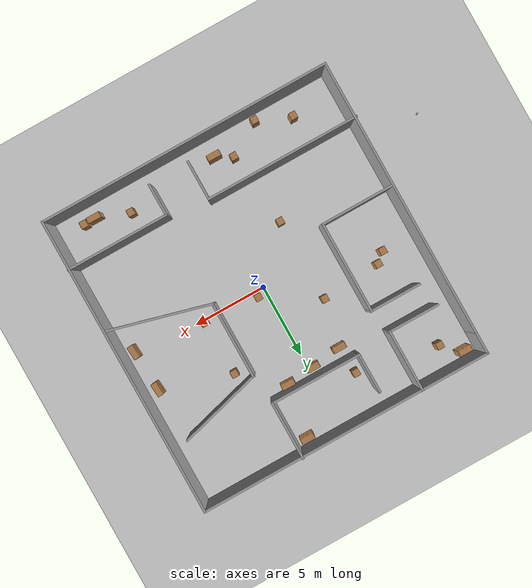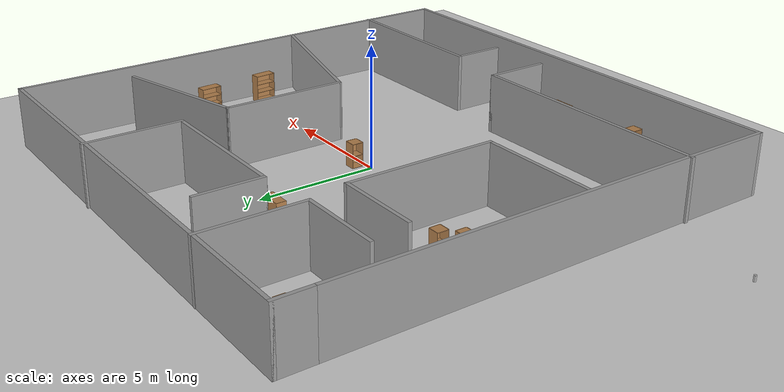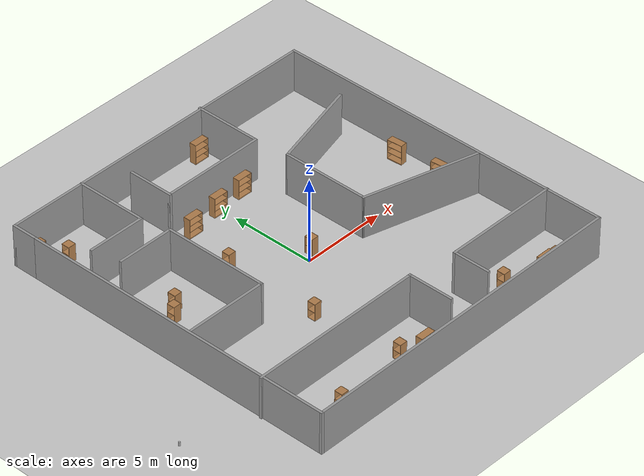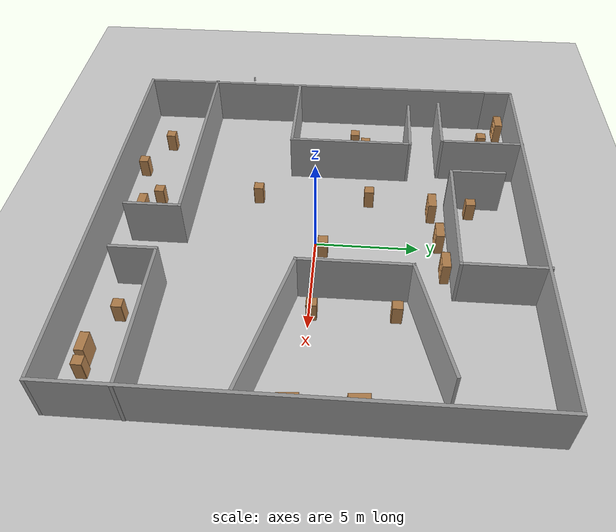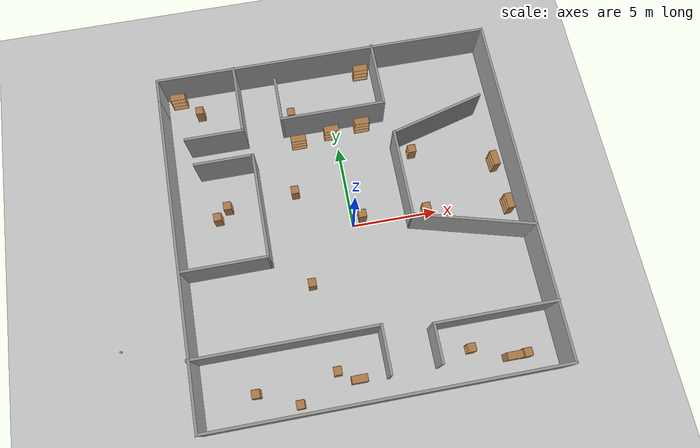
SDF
<sdf version="1.6">
 <world name="default">
  <light name="sun" type="directional">
   <pose>0 0 10 0 -0 0</pose>
   <diffuse>0.8 0.8 0.8 1</diffuse>
   <specular>0.2 0.2 0.2 1</specular>
   <attenuation>
    <range>1000</range>
    <constant>0.9</constant>
    <linear>0.01</linear>
    <quadratic>0.001</quadratic>
   </attenuation>
   <direction>-0.5 0.1 -0.9</direction>
  </light>
  <model name="ground_plane">
   <static>1</static>
   <link name="link">
    <collision name="collision">
     <geometry><plane><normal>0 0 1</normal><size>100 100</size></plane></geometry>
     <surface><friction><ode><mu>100</mu><mu2>50</mu2></ode></friction></surface>
    </collision>
    <visual name="visual">
     <cast_shadows>0</cast_shadows>
     <geometry><plane><normal>0 0 1</normal><size>100 100</size></plane></geometry>
     <material>
      <script><uri>file://media/materials/scripts/gazebo.material</uri><name>Gazebo/Grey</name></script>
     </material>
    </visual>
   </link>
  </model>
  <gravity>0 0 -9.8</gravity>
  <magnetic_field>6e-06 2.3e-05 -4.2e-05</magnetic_field>
  <atmosphere type="adiabatic"/>
  <physics name="default_physics" default="0" type="ode">
   <max_step_size>0.001</max_step_size>
   <real_time_factor>1</real_time_factor>
   <real_time_update_rate>1000</real_time_update_rate>
  </physics>
  <scene><ambient>0.4 0.4 0.4 1</ambient><background>0.7 0.7 0.7 1</background><shadows>1</shadows></scene>
  <audio><device>default</device></audio>
  <spherical_coordinates>
   <surface_model>EARTH_WGS84</surface_model>
   <latitude_deg>0</latitude_deg>
   <longitude_deg>0</longitude_deg>
   <elevation>0</elevation>
   <heading_deg>0</heading_deg>
  </spherical_coordinates>
  <model name="room">
   <pose>-0.112606 0.113774 0 0 -0 0</pose>
   <link name="Wall_11">
    <collision name="Wall_11_Collision">
     <geometry><box><size>20.5 0.15 2.5</size></box></geometry>
     <pose>0 0 1.25 0 -0 0</pose>
    </collision>
    <visual name="Wall_11_Visual">
     <pose>0 0 1.25 0 -0 0</pose>
     <geometry><box><size>20.5 0.15 2.5</size></box></geometry>
     <material>
      <script><uri>file://media/materials/scripts/gazebo.material</uri><name>Gazebo/Grey</name></script>
      <ambient>1 1 1 1</ambient>
     </material>
     <meta><layer>0</layer></meta>
    </visual>
    <pose>9.95208 -0.040419 0 0 -0 -1.5708</pose>
   </link>
   <link name="Wall_12">
    <collision name="Wall_12_Collision">
     <geometry><box><size>20 0.15 2.5</size></box></geometry>
     <pose>0 0 1.25 0 -0 0</pose>
    </collision>
    <visual name="Wall_12_Visual">
     <pose>0 0 1.25 0 -0 0</pose>
     <geometry><box><size>20 0.15 2.5</size></box></geometry>
     <material>
      <script><uri>file://media/materials/scripts/gazebo.material</uri><name>Gazebo/Grey</name></script>
      <ambient>1 1 1 1</ambient>
     </material>
     <meta><layer>0</layer></meta>
    </visual>
    <pose>0.027078 -10.2154 0 0 -0 3.14159</pose>
   </link>
   <link name="Wall_13">
    <collision name="Wall_13_Collision">
     <geometry><box><size>19 0.15 2.5</size></box></geometry>
     <pose>0 0 1.25 0 -0 0</pose>
    </collision>
    <visual name="Wall_13_Visual">
     <pose>0 0 1.25 0 -0 0</pose>
     <geometry><box><size>19 0.15 2.5</size></box></geometry>
     <material>
      <script><uri>file://media/materials/scripts/gazebo.material</uri><name>Gazebo/Grey</name></script>
      <ambient>1 1 1 1</ambient>
     </material>
     <meta><layer>0</layer></meta>
    </visual>
    <pose>-9.89792 -0.790419 0 0 -0 1.5708</pose>
   </link>
   <link name="Wall_15">
    <collision name="Wall_15_Collision">
     <geometry><box><size>7 0.15 2.5</size></box></geometry>
     <pose>0 0 1.25 0 -0 0</pose>
    </collision>
    <visual name="Wall_15_Visual">
     <pose>0 0 1.25 0 -0 0</pose>
     <geometry><box><size>7 0.15 2.5</size></box></geometry>
     <material>
      <script><uri>file://media/materials/scripts/gazebo.material</uri><name>Gazebo/Grey</name></script>
      <ambient>1 1 1 1</ambient>
     </material>
     <meta><layer>0</layer></meta>
    </visual>
    <pose>6.55322 -6.88699 0 0 -0 3.14159</pose>
   </link>
   <link name="Wall_16">
    <collision name="Wall_16_Collision">
     <geometry><box><size>2.25 0.15 2.5</size></box></geometry>
     <pose>0 0 1.25 0 -0 0</pose>
    </collision>
    <visual name="Wall_16_Visual">
     <pose>0 0 1.25 0 -0 0</pose>
     <geometry><box><size>2.25 0.15 2.5</size></box></geometry>
     <material>
      <script><uri>file://media/materials/scripts/gazebo.material</uri><name>Gazebo/Grey</name></script>
      <ambient>1 1 1 1</ambient>
     </material>
     <meta><layer>0</layer></meta>
    </visual>
    <pose>3.12822 -7.93699 0 0 -0 -1.5708</pose>
   </link>
   <link name="Wall_18">
    <collision name="Wall_18_Collision">
     <geometry><box><size>10.5 0.15 2.5</size></box></geometry>
     <pose>0 0 1.25 0 -0 0</pose>
    </collision>
    <visual name="Wall_18_Visual">
     <pose>0 0 1.25 0 -0 0</pose>
     <geometry><box><size>10.5 0.15 2.5</size></box></geometry>
     <material>
      <script><uri>file://media/materials/scripts/gazebo.material</uri><name>Gazebo/Grey</name></script>
      <ambient>1 1 1 1</ambient>
     </material>
     <meta><layer>0</layer></meta>
    </visual>
    <pose>-4.80322 -6.45897 0 0 -0 0</pose>
   </link>
   <link name="Wall_19">
    <collision name="Wall_19_Collision">
     <geometry><box><size>2.75 0.15 2.5</size></box></geometry>
     <pose>0 0 1.25 0 -0 0</pose>
    </collision>
    <visual name="Wall_19_Visual">
     <pose>0 0 1.25 0 -0 0</pose>
     <geometry><box><size>2.75 0.15 2.5</size></box></geometry>
     <material>
      <script><uri>file://media/materials/scripts/gazebo.material</uri><name>Gazebo/Grey</name></script>
      <ambient>1 1 1 1</ambient>
     </material>
     <meta><layer>0</layer></meta>
    </visual>
    <pose>0.371783 -7.75897 0 0 -0 -1.5708</pose>
   </link>
   <link name="Wall_21">
    <collision name="Wall_21_Collision">
     <geometry><box><size>5 0.15 2.5</size></box></geometry>
     <pose>0 0 1.25 0 -0 0</pose>
    </collision>
    <visual name="Wall_21_Visual">
     <pose>0 0 1.25 0 -0 0</pose>
     <geometry><box><size>5 0.15 2.5</size></box></geometry>
     <material>
      <script><uri>file://media/materials/scripts/gazebo.material</uri><name>Gazebo/Grey</name></script>
      <ambient>1 1 1 1</ambient>
     </material>
     <meta><layer>0</layer></meta>
    </visual>
    <pose>-7.39271 -1.69725 0 0 -0 0</pose>
   </link>
   <link name="Wall_22">
    <collision name="Wall_22_Collision">
     <geometry><box><size>6.25 0.15 2.5</size></box></geometry>
     <pose>0 0 1.25 0 -0 0</pose>
    </collision>
    <visual name="Wall_22_Visual">
     <pose>0 0 1.25 0 -0 0</pose>
     <geometry><box><size>6.25 0.15 2.5</size></box></geometry>
     <material>
      <script><uri>file://media/materials/scripts/gazebo.material</uri><name>Gazebo/Grey</name></script>
      <ambient>1 1 1 1</ambient>
     </material>
     <meta><layer>0</layer></meta>
    </visual>
    <pose>-4.96771 1.35275 0 0 -0 1.5708</pose>
   </link>
   <link name="Wall_23">
    <collision name="Wall_23_Collision">
     <geometry><box><size>3.5 0.15 2.5</size></box></geometry>
     <pose>0 0 1.25 0 -0 0</pose>
    </collision>
    <visual name="Wall_23_Visual">
     <pose>0 0 1.25 0 -0 0</pose>
     <geometry><box><size>3.5 0.15 2.5</size></box></geometry>
     <material>
      <script><uri>file://media/materials/scripts/gazebo.material</uri><name>Gazebo/Grey</name></script>
      <ambient>1 1 1 1</ambient>
     </material>
     <meta><layer>0</layer></meta>
    </visual>
    <pose>-6.64271 4.40275 0 0 -0 3.14159</pose>
   </link>
   <link name="Wall_26">
    <collision name="Wall_26_Collision">
     <geometry><box><size>4.25 0.15 2.5</size></box></geometry>
     <pose>0 0 1.25 0 -0 0</pose>
    </collision>
    <visual name="Wall_26_Visual">
     <pose>0 0 1.25 0 -0 0</pose>
     <geometry><box><size>4.25 0.15 2.5</size></box></geometry>
     <material>
      <script><uri>file://media/materials/scripts/gazebo.material</uri><name>Gazebo/Grey</name></script>
      <ambient>1 1 1 1</ambient>
     </material>
     <meta><layer>0</layer></meta>
    </visual>
    <pose>-5.3243 8.10389 0 0 -0 -1.5708</pose>
   </link>
   <link name="Wall_27">
    <collision name="Wall_27_Collision">
     <geometry><box><size>3.5 0.15 2.5</size></box></geometry>
     <pose>0 0 1.25 0 -0 0</pose>
    </collision>
    <visual name="Wall_27_Visual">
     <pose>0 0 1.25 0 -0 0</pose>
     <geometry><box><size>3.5 0.15 2.5</size></box></geometry>
     <material>
      <script><uri>file://media/materials/scripts/gazebo.material</uri><name>Gazebo/Grey</name></script>
      <ambient>1 1 1 1</ambient>
     </material>
     <meta><layer>0</layer></meta>
    </visual>
    <pose>-6.9993 6.05389 0 0 -0 3.14159</pose>
   </link>
   <link name="Wall_29">
    <collision name="Wall_29_Collision">
     <geometry><box><size>7 0.15 2.5</size></box></geometry>
     <pose>0 0 1.25 0 -0 0</pose>
    </collision>
    <visual name="Wall_29_Visual">
     <pose>0 0 1.25 0 -0 0</pose>
     <geometry><box><size>7 0.15 2.5</size></box></geometry>
     <material>
      <script><uri>file://media/materials/scripts/gazebo.material</uri><name>Gazebo/Grey</name></script>
      <ambient>1 1 1 1</ambient>
     </material>
     <meta><layer>0</layer></meta>
    </visual>
    <pose>6.62632 -1.63439 0 0 -0 2.87979</pose>
   </link>
   <link name="Wall_30">
    <collision name="Wall_30_Collision">
     <geometry><box><size>5.25 0.15 2.5</size></box></geometry>
     <pose>0 0 1.25 0 -0 0</pose>
    </collision>
    <visual name="Wall_30_Visual">
     <pose>0 0 1.25 0 -0 0</pose>
     <geometry><box><size>5.25 0.15 2.5</size></box></geometry>
     <material>
      <script><uri>file://media/materials/scripts/gazebo.material</uri><name>Gazebo/Grey</name></script>
      <ambient>1 1 1 1</ambient>
     </material>
     <meta><layer>0</layer></meta>
    </visual>
    <pose>3.31803 1.80206 0 0 -0 1.5708</pose>
   </link>
   <link name="Wall_31">
    <collision name="Wall_31_Collision">
     <geometry><box><size>5.75 0.15 2.5</size></box></geometry>
     <pose>0 0 1.25 0 -0 0</pose>
    </collision>
    <visual name="Wall_31_Visual">
     <pose>0 0 1.25 0 -0 0</pose>
     <geometry><box><size>5.75 0.15 2.5</size></box></geometry>
     <material>
      <script><uri>file://media/materials/scripts/gazebo.material</uri><name>Gazebo/Grey</name></script>
      <ambient>1 1 1 1</ambient>
     </material>
     <meta><layer>0</layer></meta>
    </visual>
    <pose>6.02262 5.07676 0 0 -0 0.261799</pose>
   </link>
   <link name="Wall_33">
    <collision name="Wall_33_Collision">
     <geometry><box><size>4 0.15 2.5</size></box></geometry>
     <pose>0 0 1.25 0 -0 0</pose>
    </collision>
    <visual name="Wall_33_Visual">
     <pose>0 0 1.25 0 -0 0</pose>
     <geometry><box><size>4 0.15 2.5</size></box></geometry>
     <material>
      <script><uri>file://media/materials/scripts/gazebo.material</uri><name>Gazebo/Grey</name></script>
      <ambient>1 1 1 1</ambient>
     </material>
     <meta><layer>0</layer></meta>
    </visual>
    <pose>3.10502 8.29042 0 0 -0 -1.5708</pose>
   </link>
   <link name="Wall_34">
    <collision name="Wall_34_Collision">
     <geometry><box><size>6.25 0.15 2.5</size></box></geometry>
     <pose>0 0 1.25 0 -0 0</pose>
    </collision>
    <visual name="Wall_34_Visual">
     <pose>0 0 1.25 0 -0 0</pose>
     <geometry><box><size>6.25 0.15 2.5</size></box></geometry>
     <material>
      <script><uri>file://media/materials/scripts/gazebo.material</uri><name>Gazebo/Grey</name></script>
      <ambient>1 1 1 1</ambient>
     </material>
     <meta><layer>0</layer></meta>
    </visual>
    <pose>0.055024 6.36542 0 0 -0 3.14159</pose>
   </link>
   <link name="Wall_35">
    <collision name="Wall_35_Collision">
     <geometry><box><size>2.75 0.15 2.5</size></box></geometry>
     <pose>0 0 1.25 0 -0 0</pose>
    </collision>
    <visual name="Wall_35_Visual">
     <pose>0 0 1.25 0 -0 0</pose>
     <geometry><box><size>2.75 0.15 2.5</size></box></geometry>
     <material>
      <script><uri>file://media/materials/scripts/gazebo.material</uri><name>Gazebo/Grey</name></script>
      <ambient>1 1 1 1</ambient>
     </material>
     <meta><layer>0</layer></meta>
    </visual>
    <pose>-2.99498 7.66542 0 0 -0 1.5708</pose>
   </link>
   <link name="Wall_5">
    <collision name="Wall_5_Collision">
     <geometry><box><size>1.5 0.15 2.5</size></box></geometry>
     <pose>0 0 1.25 0 -0 0</pose>
    </collision>
    <visual name="Wall_5_Visual">
     <pose>0 0 1.25 0 -0 0</pose>
     <geometry><box><size>1.5 0.15 2.5</size></box></geometry>
     <material>
      <script><uri>file://media/materials/scripts/gazebo.material</uri><name>Gazebo/Grey</name></script>
      <ambient>1 1 1 1</ambient>
     </material>
     <meta><layer>0</layer></meta>
    </visual>
    <pose>-9.89792 9.45958 0 0 -0 1.5708</pose>
   </link>
   <link name="Wall_7">
    <collision name="Wall_7_Collision">
     <geometry><box><size>20 0.15 2.5</size></box></geometry>
     <pose>0 0 1.25 0 -0 0</pose>
    </collision>
    <visual name="Wall_7_Visual">
     <pose>0 0 1.25 0 -0 0</pose>
     <geometry><box><size>20 0.15 2.5</size></box></geometry>
     <material>
      <script><uri>file://media/materials/scripts/gazebo.material</uri><name>Gazebo/Grey</name></script>
      <ambient>1 1 1 1</ambient>
     </material>
     <meta><layer>0</layer></meta>
    </visual>
    <pose>0.027078 10.1346 0 0 -0 0</pose>
   </link>
   <static>1</static>
  </model>
  <model name="beer">
   <link name="link">
    <pose>0 0 0.115 0 -0 0</pose>
    <inertial>
     <mass>0.39</mass>
     <inertia><ixx>0.00058</ixx><ixy>0</ixy><ixz>0</ixz><iyy>0.00058</iyy><iyz>0</iyz><izz>0.00019</izz></inertia>
    </inertial>
    <collision name="collision">
     <geometry><cylinder><radius>0.055</radius><length>0.23</length></cylinder></geometry>
    </collision>
    <visual name="visual">
     <geometry><cylinder><radius>0.055</radius><length>0.23</length></cylinder></geometry>
     <material>
      <script>
       <uri>model://beer/materials/scripts</uri>
       <uri>model://beer/materials/textures</uri>
       <name>Beer/Diffuse</name>
      </script>
     </material>
    </visual>
   </link>
   <pose>-14.1156 -4.90296 -2e-06 1e-06 0 -4.1e-05</pose>
  </model>
  <model name="bookshelf">
   <static>1</static>
   <link name="link">
    <inertial><mass>1</mass></inertial>
    <collision name="back">
     <pose>0 0.005 0.6 0 -0 0</pose>
     <geometry><box><size>0.9 0.01 1.2</size></box></geometry>
    </collision>
    <visual name="visual1">
     <pose>0 0.005 0.6 0 -0 0</pose>
     <geometry><box><size>0.9 0.01 1.2</size></box></geometry>
     <material>
      <script><uri>file://media/materials/scripts/gazebo.material</uri><name>Gazebo/Wood</name></script>
     </material>
    </visual>
    <collision name="left_side">
     <pose>0.45 -0.195 0.6 0 -0 0</pose>
     <geometry><box><size>0.02 0.4 1.2</size></box></geometry>
    </collision>
    <visual name="visual2">
     <pose>0.45 -0.195 0.6 0 -0 0</pose>
     <geometry><box><size>0.02 0.4 1.2</size></box></geometry>
     <material>
      <script><uri>file://media/materials/scripts/gazebo.material</uri><name>Gazebo/Wood</name></script>
     </material>
    </visual>
    <collision name="right_side">
     <pose>-0.45 -0.195 0.6 0 -0 0</pose>
     <geometry><box><size>0.02 0.4 1.2</size></box></geometry>
    </collision>
    <visual name="visual3">
     <pose>-0.45 -0.195 0.6 0 -0 0</pose>
     <geometry><box><size>0.02 0.4 1.2</size></box></geometry>
     <material>
      <script><uri>file://media/materials/scripts/gazebo.material</uri><name>Gazebo/Wood</name></script>
     </material>
    </visual>
    <collision name="bottom">
     <pose>0 -0.195 0.03 0 -0 0</pose>
     <geometry><box><size>0.88 0.4 0.06</size></box></geometry>
    </collision>
    <visual name="visual4">
     <pose>0 -0.195 0.03 0 -0 0</pose>
     <geometry><box><size>0.88 0.4 0.06</size></box></geometry>
     <material>
      <script><uri>file://media/materials/scripts/gazebo.material</uri><name>Gazebo/Wood</name></script>
     </material>
    </visual>
    <collision name="top">
     <pose>0 -0.195 1.19 0 -0 0</pose>
     <geometry><box><size>0.88 0.4 0.02</size></box></geometry>
    </collision>
    <visual name="visual5">
     <pose>0 -0.195 1.19 0 -0 0</pose>
     <geometry><box><size>0.88 0.4 0.02</size></box></geometry>
     <material>
      <script><uri>file://media/materials/scripts/gazebo.material</uri><name>Gazebo/Wood</name></script>
     </material>
    </visual>
    <collision name="low_shelf">
     <pose>0 -0.195 0.43 0 -0 0</pose>
     <geometry><box><size>0.88 0.4 0.02</size></box></geometry>
    </collision>
    <visual name="visual6">
     <pose>0 -0.195 0.43 0 -0 0</pose>
     <geometry><box><size>0.88 0.4 0.02</size></box></geometry>
     <material>
      <script><uri>file://media/materials/scripts/gazebo.material</uri><name>Gazebo/Wood</name></script>
     </material>
    </visual>
    <collision name="high_shelf">
     <pose>0 -0.195 0.8 0 -0 0</pose>
     <geometry><box><size>0.88 0.4 0.02</size></box></geometry>
    </collision>
    <visual name="visual7">
     <pose>0 -0.195 0.8 0 -0 0</pose>
     <geometry><box><size>0.88 0.4 0.02</size></box></geometry>
     <material>
      <script><uri>file://media/materials/scripts/gazebo.material</uri><name>Gazebo/Wood</name></script>
     </material>
    </visual>
   </link>
   <pose>1.63154 6.3022 0 0 -0 0</pose>
  </model>
  <model name="bookshelf_0">
   <static>1</static>
   <link name="link">
    <inertial><mass>1</mass></inertial>
    <collision name="back">
     <pose>0 0.005 0.6 0 -0 0</pose>
     <geometry><box><size>0.9 0.01 1.2</size></box></geometry>
    </collision>
    <visual name="visual1">
     <pose>0 0.005 0.6 0 -0 0</pose>
     <geometry><box><size>0.9 0.01 1.2</size></box></geometry>
     <material>
      <script><uri>file://media/materials/scripts/gazebo.material</uri><name>Gazebo/Wood</name></script>
     </material>
    </visual>
    <collision name="left_side">
     <pose>0.45 -0.195 0.6 0 -0 0</pose>
     <geometry><box><size>0.02 0.4 1.2</size></box></geometry>
    </collision>
    <visual name="visual2">
     <pose>0.45 -0.195 0.6 0 -0 0</pose>
     <geometry><box><size>0.02 0.4 1.2</size></box></geometry>
     <material>
      <script><uri>file://media/materials/scripts/gazebo.material</uri><name>Gazebo/Wood</name></script>
     </material>
    </visual>
    <collision name="right_side">
     <pose>-0.45 -0.195 0.6 0 -0 0</pose>
     <geometry><box><size>0.02 0.4 1.2</size></box></geometry>
    </collision>
    <visual name="visual3">
     <pose>-0.45 -0.195 0.6 0 -0 0</pose>
     <geometry><box><size>0.02 0.4 1.2</size></box></geometry>
     <material>
      <script><uri>file://media/materials/scripts/gazebo.material</uri><name>Gazebo/Wood</name></script>
     </material>
    </visual>
    <collision name="bottom">
     <pose>0 -0.195 0.03 0 -0 0</pose>
     <geometry><box><size>0.88 0.4 0.06</size></box></geometry>
    </collision>
    <visual name="visual4">
     <pose>0 -0.195 0.03 0 -0 0</pose>
     <geometry><box><size>0.88 0.4 0.06</size></box></geometry>
     <material>
      <script><uri>file://media/materials/scripts/gazebo.material</uri><name>Gazebo/Wood</name></script>
     </material>
    </visual>
    <collision name="top">
     <pose>0 -0.195 1.19 0 -0 0</pose>
     <geometry><box><size>0.88 0.4 0.02</size></box></geometry>
    </collision>
    <visual name="visual5">
     <pose>0 -0.195 1.19 0 -0 0</pose>
     <geometry><box><size>0.88 0.4 0.02</size></box></geometry>
     <material>
      <script><uri>file://media/materials/scripts/gazebo.material</uri><name>Gazebo/Wood</name></script>
     </material>
    </visual>
    <collision name="low_shelf">
     <pose>0 -0.195 0.43 0 -0 0</pose>
     <geometry><box><size>0.88 0.4 0.02</size></box></geometry>
    </collision>
    <visual name="visual6">
     <pose>0 -0.195 0.43 0 -0 0</pose>
     <geometry><box><size>0.88 0.4 0.02</size></box></geometry>
     <material>
      <script><uri>file://media/materials/scripts/gazebo.material</uri><name>Gazebo/Wood</name></script>
     </material>
    </visual>
    <collision name="high_shelf">
     <pose>0 -0.195 0.8 0 -0 0</pose>
     <geometry><box><size>0.88 0.4 0.02</size></box></geometry>
    </collision>
    <visual name="visual7">
     <pose>0 -0.195 0.8 0 -0 0</pose>
     <geometry><box><size>0.88 0.4 0.02</size></box></geometry>
     <material>
      <script><uri>file://media/materials/scripts/gazebo.material</uri><name>Gazebo/Wood</name></script>
     </material>
    </visual>
   </link>
   <pose>-0.266671 6.13176 0 0 -0 0</pose>
  </model>
  <model name="bookshelf_1">
   <static>1</static>
   <link name="link">
    <inertial><mass>1</mass></inertial>
    <collision name="back">
     <pose>0 0.005 0.6 0 -0 0</pose>
     <geometry><box><size>0.9 0.01 1.2</size></box></geometry>
    </collision>
    <visual name="visual1">
     <pose>0 0.005 0.6 0 -0 0</pose>
     <geometry><box><size>0.9 0.01 1.2</size></box></geometry>
     <material>
      <script><uri>file://media/materials/scripts/gazebo.material</uri><name>Gazebo/Wood</name></script>
     </material>
    </visual>
    <collision name="left_side">
     <pose>0.45 -0.195 0.6 0 -0 0</pose>
     <geometry><box><size>0.02 0.4 1.2</size></box></geometry>
    </collision>
    <visual name="visual2">
     <pose>0.45 -0.195 0.6 0 -0 0</pose>
     <geometry><box><size>0.02 0.4 1.2</size></box></geometry>
     <material>
      <script><uri>file://media/materials/scripts/gazebo.material</uri><name>Gazebo/Wood</name></script>
     </material>
    </visual>
    <collision name="right_side">
     <pose>-0.45 -0.195 0.6 0 -0 0</pose>
     <geometry><box><size>0.02 0.4 1.2</size></box></geometry>
    </collision>
    <visual name="visual3">
     <pose>-0.45 -0.195 0.6 0 -0 0</pose>
     <geometry><box><size>0.02 0.4 1.2</size></box></geometry>
     <material>
      <script><uri>file://media/materials/scripts/gazebo.material</uri><name>Gazebo/Wood</name></script>
     </material>
    </visual>
    <collision name="bottom">
     <pose>0 -0.195 0.03 0 -0 0</pose>
     <geometry><box><size>0.88 0.4 0.06</size></box></geometry>
    </collision>
    <visual name="visual4">
     <pose>0 -0.195 0.03 0 -0 0</pose>
     <geometry><box><size>0.88 0.4 0.06</size></box></geometry>
     <material>
      <script><uri>file://media/materials/scripts/gazebo.material</uri><name>Gazebo/Wood</name></script>
     </material>
    </visual>
    <collision name="top">
     <pose>0 -0.195 1.19 0 -0 0</pose>
     <geometry><box><size>0.88 0.4 0.02</size></box></geometry>
    </collision>
    <visual name="visual5">
     <pose>0 -0.195 1.19 0 -0 0</pose>
     <geometry><box><size>0.88 0.4 0.02</size></box></geometry>
     <material>
      <script><uri>file://media/materials/scripts/gazebo.material</uri><name>Gazebo/Wood</name></script>
     </material>
    </visual>
    <collision name="low_shelf">
     <pose>0 -0.195 0.43 0 -0 0</pose>
     <geometry><box><size>0.88 0.4 0.02</size></box></geometry>
    </collision>
    <visual name="visual6">
     <pose>0 -0.195 0.43 0 -0 0</pose>
     <geometry><box><size>0.88 0.4 0.02</size></box></geometry>
     <material>
      <script><uri>file://media/materials/scripts/gazebo.material</uri><name>Gazebo/Wood</name></script>
     </material>
    </visual>
    <collision name="high_shelf">
     <pose>0 -0.195 0.8 0 -0 0</pose>
     <geometry><box><size>0.88 0.4 0.02</size></box></geometry>
    </collision>
    <visual name="visual7">
     <pose>0 -0.195 0.8 0 -0 0</pose>
     <geometry><box><size>0.88 0.4 0.02</size></box></geometry>
     <material>
      <script><uri>file://media/materials/scripts/gazebo.material</uri><name>Gazebo/Wood</name></script>
     </material>
    </visual>
   </link>
   <pose>-2.31915 5.86151 0 0 -0 0</pose>
  </model>
  <model name="cabinet">
   <static>1</static>
   <link name="cabinet_bottom_plate">
    <inertial>
     <pose>0 0 -1 0 -0 0</pose>
     <inertia><ixx>2.05</ixx><ixy>0</ixy><ixz>0</ixz><iyy>2.05</iyy><iyz>0</iyz><izz>2.05</izz></inertia>
     <mass>25</mass>
    </inertial>
    <collision name="cabinet_bottom_plate_geom">
     <pose>0 0 0.01 0 -0 0</pose>
     <geometry><box><size>0.45 0.45 0.02</size></box></geometry>
    </collision>
    <visual name="cabinet_bottom_plate_geom_visual">
     <pose>0 0 0.01 0 -0 0</pose>
     <geometry><box><size>0.45 0.45 0.02</size></box></geometry>
     <material>
      <script><uri>file://media/materials/scripts/gazebo.material</uri><name>Gazebo/Wood</name></script>
     </material>
    </visual>
    <collision name="cabinet_bottom_plate_geom_cabinet_back_plate">
     <pose>0.235 0 0.51 0 -0 0</pose>
     <geometry><box><size>0.02 0.45 1.02</size></box></geometry>
    </collision>
    <visual name="cabinet_bottom_plate_geom_cabinet_back_plate_visual">
     <pose>0.235 0 0.51 0 -0 0</pose>
     <geometry><box><size>0.02 0.45 1.02</size></box></geometry>
     <material>
      <script><uri>file://media/materials/scripts/gazebo.material</uri><name>Gazebo/Wood</name></script>
     </material>
    </visual>
    <collision name="cabinet_bottom_plate_geom_cabinet_left_plate">
     <pose>0 0.235 0.51 0 -0 0</pose>
     <geometry><box><size>0.45 0.02 1.02</size></box></geometry>
    </collision>
    <visual name="cabinet_bottom_plate_geom_cabinet_left_plate_visual">
     <pose>0 0.235 0.51 0 -0 0</pose>
     <geometry><box><size>0.45 0.02 1.02</size></box></geometry>
     <material>
      <script><uri>file://media/materials/scripts/gazebo.material</uri><name>Gazebo/Wood</name></script>
     </material>
    </visual>
    <collision name="cabinet_bottom_plate_geom_cabinet_middle_plate">
     <pose>0 0 0.51 0 -0 0</pose>
     <geometry><box><size>0.45 0.45 0.02</size></box></geometry>
    </collision>
    <visual name="cabinet_bottom_plate_geom_cabinet_middle_plate_visual">
     <pose>0 0 0.51 0 -0 0</pose>
     <geometry><box><size>0.45 0.45 0.02</size></box></geometry>
     <material>
      <script><uri>file://media/materials/scripts/gazebo.material</uri><name>Gazebo/Wood</name></script>
     </material>
    </visual>
    <collision name="cabinet_bottom_plate_geom_cabinet_right_plate">
     <pose>0 -0.235 0.51 0 -0 0</pose>
     <geometry><box><size>0.45 0.02 1.02</size></box></geometry>
    </collision>
    <visual name="cabinet_bottom_plate_geom_cabinet_right_plate_visual">
     <pose>0 -0.235 0.51 0 -0 0</pose>
     <geometry><box><size>0.45 0.02 1.02</size></box></geometry>
     <material>
      <script><uri>file://media/materials/scripts/gazebo.material</uri><name>Gazebo/Wood</name></script>
     </material>
    </visual>
    <collision name="cabinet_bottom_plate_geom_cabinet_top_plate">
     <pose>0 0 1.01 0 -0 0</pose>
     <geometry><box><size>0.45 0.45 0.02</size></box></geometry>
    </collision>
    <visual name="cabinet_bottom_plate_geom_cabinet_top_plate_visual">
     <pose>0 0 1.01 0 -0 0</pose>
     <geometry><box><size>0.45 0.45 0.02</size></box></geometry>
     <material>
      <script><uri>file://media/materials/scripts/gazebo.material</uri><name>Gazebo/Wood</name></script>
     </material>
    </visual>
   </link>
   <pose>-2.98762 -3.11503 0 0 -0 0</pose>
  </model>
  <model name="cabinet_0">
   <static>1</static>
   <link name="cabinet_bottom_plate">
    <inertial>
     <pose>0 0 -1 0 -0 0</pose>
     <inertia><ixx>2.05</ixx><ixy>0</ixy><ixz>0</ixz><iyy>2.05</iyy><iyz>0</iyz><izz>2.05</izz></inertia>
     <mass>25</mass>
    </inertial>
    <collision name="cabinet_bottom_plate_geom">
     <pose>0 0 0.01 0 -0 0</pose>
     <geometry><box><size>0.45 0.45 0.02</size></box></geometry>
    </collision>
    <visual name="cabinet_bottom_plate_geom_visual">
     <pose>0 0 0.01 0 -0 0</pose>
     <geometry><box><size>0.45 0.45 0.02</size></box></geometry>
     <material>
      <script><uri>file://media/materials/scripts/gazebo.material</uri><name>Gazebo/Wood</name></script>
     </material>
    </visual>
    <collision name="cabinet_bottom_plate_geom_cabinet_back_plate">
     <pose>0.235 0 0.51 0 -0 0</pose>
     <geometry><box><size>0.02 0.45 1.02</size></box></geometry>
    </collision>
    <visual name="cabinet_bottom_plate_geom_cabinet_back_plate_visual">
     <pose>0.235 0 0.51 0 -0 0</pose>
     <geometry><box><size>0.02 0.45 1.02</size></box></geometry>
     <material>
      <script><uri>file://media/materials/scripts/gazebo.material</uri><name>Gazebo/Wood</name></script>
     </material>
    </visual>
    <collision name="cabinet_bottom_plate_geom_cabinet_left_plate">
     <pose>0 0.235 0.51 0 -0 0</pose>
     <geometry><box><size>0.45 0.02 1.02</size></box></geometry>
    </collision>
    <visual name="cabinet_bottom_plate_geom_cabinet_left_plate_visual">
     <pose>0 0.235 0.51 0 -0 0</pose>
     <geometry><box><size>0.45 0.02 1.02</size></box></geometry>
     <material>
      <script><uri>file://media/materials/scripts/gazebo.material</uri><name>Gazebo/Wood</name></script>
     </material>
    </visual>
    <collision name="cabinet_bottom_plate_geom_cabinet_middle_plate">
     <pose>0 0 0.51 0 -0 0</pose>
     <geometry><box><size>0.45 0.45 0.02</size></box></geometry>
    </collision>
    <visual name="cabinet_bottom_plate_geom_cabinet_middle_plate_visual">
     <pose>0 0 0.51 0 -0 0</pose>
     <geometry><box><size>0.45 0.45 0.02</size></box></geometry>
     <material>
      <script><uri>file://media/materials/scripts/gazebo.material</uri><name>Gazebo/Wood</name></script>
     </material>
    </visual>
    <collision name="cabinet_bottom_plate_geom_cabinet_right_plate">
     <pose>0 -0.235 0.51 0 -0 0</pose>
     <geometry><box><size>0.45 0.02 1.02</size></box></geometry>
    </collision>
    <visual name="cabinet_bottom_plate_geom_cabinet_right_plate_visual">
     <pose>0 -0.235 0.51 0 -0 0</pose>
     <geometry><box><size>0.45 0.02 1.02</size></box></geometry>
     <material>
      <script><uri>file://media/materials/scripts/gazebo.material</uri><name>Gazebo/Wood</name></script>
     </material>
    </visual>
    <collision name="cabinet_bottom_plate_geom_cabinet_top_plate">
     <pose>0 0 1.01 0 -0 0</pose>
     <geometry><box><size>0.45 0.45 0.02</size></box></geometry>
    </collision>
    <visual name="cabinet_bottom_plate_geom_cabinet_top_plate_visual">
     <pose>0 0 1.01 0 -0 0</pose>
     <geometry><box><size>0.45 0.45 0.02</size></box></geometry>
     <material>
      <script><uri>file://media/materials/scripts/gazebo.material</uri><name>Gazebo/Wood</name></script>
     </material>
    </visual>
   </link>
   <pose>0.574896 0.397613 0 0 -0 0</pose>
  </model>
  <model name="cabinet_1">
   <static>1</static>
   <link name="cabinet_bottom_plate">
    <inertial>
     <pose>0 0 -1 0 -0 0</pose>
     <inertia><ixx>2.05</ixx><ixy>0</ixy><ixz>0</ixz><iyy>2.05</iyy><iyz>0</iyz><izz>2.05</izz></inertia>
     <mass>25</mass>
    </inertial>
    <collision name="cabinet_bottom_plate_geom">
     <pose>0 0 0.01 0 -0 0</pose>
     <geometry><box><size>0.45 0.45 0.02</size></box></geometry>
    </collision>
    <visual name="cabinet_bottom_plate_geom_visual">
     <pose>0 0 0.01 0 -0 0</pose>
     <geometry><box><size>0.45 0.45 0.02</size></box></geometry>
     <material>
      <script><uri>file://media/materials/scripts/gazebo.material</uri><name>Gazebo/Wood</name></script>
     </material>
    </visual>
    <collision name="cabinet_bottom_plate_geom_cabinet_back_plate">
     <pose>0.235 0 0.51 0 -0 0</pose>
     <geometry><box><size>0.02 0.45 1.02</size></box></geometry>
    </collision>
    <visual name="cabinet_bottom_plate_geom_cabinet_back_plate_visual">
     <pose>0.235 0 0.51 0 -0 0</pose>
     <geometry><box><size>0.02 0.45 1.02</size></box></geometry>
     <material>
      <script><uri>file://media/materials/scripts/gazebo.material</uri><name>Gazebo/Wood</name></script>
     </material>
    </visual>
    <collision name="cabinet_bottom_plate_geom_cabinet_left_plate">
     <pose>0 0.235 0.51 0 -0 0</pose>
     <geometry><box><size>0.45 0.02 1.02</size></box></geometry>
    </collision>
    <visual name="cabinet_bottom_plate_geom_cabinet_left_plate_visual">
     <pose>0 0.235 0.51 0 -0 0</pose>
     <geometry><box><size>0.45 0.02 1.02</size></box></geometry>
     <material>
      <script><uri>file://media/materials/scripts/gazebo.material</uri><name>Gazebo/Wood</name></script>
     </material>
    </visual>
    <collision name="cabinet_bottom_plate_geom_cabinet_middle_plate">
     <pose>0 0 0.51 0 -0 0</pose>
     <geometry><box><size>0.45 0.45 0.02</size></box></geometry>
    </collision>
    <visual name="cabinet_bottom_plate_geom_cabinet_middle_plate_visual">
     <pose>0 0 0.51 0 -0 0</pose>
     <geometry><box><size>0.45 0.45 0.02</size></box></geometry>
     <material>
      <script><uri>file://media/materials/scripts/gazebo.material</uri><name>Gazebo/Wood</name></script>
     </material>
    </visual>
    <collision name="cabinet_bottom_plate_geom_cabinet_right_plate">
     <pose>0 -0.235 0.51 0 -0 0</pose>
     <geometry><box><size>0.45 0.02 1.02</size></box></geometry>
    </collision>
    <visual name="cabinet_bottom_plate_geom_cabinet_right_plate_visual">
     <pose>0 -0.235 0.51 0 -0 0</pose>
     <geometry><box><size>0.45 0.02 1.02</size></box></geometry>
     <material>
      <script><uri>file://media/materials/scripts/gazebo.material</uri><name>Gazebo/Wood</name></script>
     </material>
    </visual>
    <collision name="cabinet_bottom_plate_geom_cabinet_top_plate">
     <pose>0 0 1.01 0 -0 0</pose>
     <geometry><box><size>0.45 0.45 0.02</size></box></geometry>
    </collision>
    <visual name="cabinet_bottom_plate_geom_cabinet_top_plate_visual">
     <pose>0 0 1.01 0 -0 0</pose>
     <geometry><box><size>0.45 0.45 0.02</size></box></geometry>
     <material>
      <script><uri>file://media/materials/scripts/gazebo.material</uri><name>Gazebo/Wood</name></script>
     </material>
    </visual>
   </link>
   <pose>-3.05665 2.53564 0 0 -0 0</pose>
  </model>
  <model name="cabinet_2">
   <static>1</static>
   <link name="cabinet_bottom_plate">
    <inertial>
     <pose>0 0 -1 0 -0 0</pose>
     <inertia><ixx>2.05</ixx><ixy>0</ixy><ixz>0</ixz><iyy>2.05</iyy><iyz>0</iyz><izz>2.05</izz></inertia>
     <mass>25</mass>
    </inertial>
    <collision name="cabinet_bottom_plate_geom">
     <pose>0 0 0.01 0 -0 0</pose>
     <geometry><box><size>0.45 0.45 0.02</size></box></geometry>
    </collision>
    <visual name="cabinet_bottom_plate_geom_visual">
     <pose>0 0 0.01 0 -0 0</pose>
     <geometry><box><size>0.45 0.45 0.02</size></box></geometry>
     <material>
      <script><uri>file://media/materials/scripts/gazebo.material</uri><name>Gazebo/Wood</name></script>
     </material>
    </visual>
    <collision name="cabinet_bottom_plate_geom_cabinet_back_plate">
     <pose>0.235 0 0.51 0 -0 0</pose>
     <geometry><box><size>0.02 0.45 1.02</size></box></geometry>
    </collision>
    <visual name="cabinet_bottom_plate_geom_cabinet_back_plate_visual">
     <pose>0.235 0 0.51 0 -0 0</pose>
     <geometry><box><size>0.02 0.45 1.02</size></box></geometry>
     <material>
      <script><uri>file://media/materials/scripts/gazebo.material</uri><name>Gazebo/Wood</name></script>
     </material>
    </visual>
    <collision name="cabinet_bottom_plate_geom_cabinet_left_plate">
     <pose>0 0.235 0.51 0 -0 0</pose>
     <geometry><box><size>0.45 0.02 1.02</size></box></geometry>
    </collision>
    <visual name="cabinet_bottom_plate_geom_cabinet_left_plate_visual">
     <pose>0 0.235 0.51 0 -0 0</pose>
     <geometry><box><size>0.45 0.02 1.02</size></box></geometry>
     <material>
      <script><uri>file://media/materials/scripts/gazebo.material</uri><name>Gazebo/Wood</name></script>
     </material>
    </visual>
    <collision name="cabinet_bottom_plate_geom_cabinet_middle_plate">
     <pose>0 0 0.51 0 -0 0</pose>
     <geometry><box><size>0.45 0.45 0.02</size></box></geometry>
    </collision>
    <visual name="cabinet_bottom_plate_geom_cabinet_middle_plate_visual">
     <pose>0 0 0.51 0 -0 0</pose>
     <geometry><box><size>0.45 0.45 0.02</size></box></geometry>
     <material>
      <script><uri>file://media/materials/scripts/gazebo.material</uri><name>Gazebo/Wood</name></script>
     </material>
    </visual>
    <collision name="cabinet_bottom_plate_geom_cabinet_right_plate">
     <pose>0 -0.235 0.51 0 -0 0</pose>
     <geometry><box><size>0.45 0.02 1.02</size></box></geometry>
    </collision>
    <visual name="cabinet_bottom_plate_geom_cabinet_right_plate_visual">
     <pose>0 -0.235 0.51 0 -0 0</pose>
     <geometry><box><size>0.45 0.02 1.02</size></box></geometry>
     <material>
      <script><uri>file://media/materials/scripts/gazebo.material</uri><name>Gazebo/Wood</name></script>
     </material>
    </visual>
    <collision name="cabinet_bottom_plate_geom_cabinet_top_plate">
     <pose>0 0 1.01 0 -0 0</pose>
     <geometry><box><size>0.45 0.45 0.02</size></box></geometry>
    </collision>
    <visual name="cabinet_bottom_plate_geom_cabinet_top_plate_visual">
     <pose>0 0 1.01 0 -0 0</pose>
     <geometry><box><size>0.45 0.45 0.02</size></box></geometry>
     <material>
      <script><uri>file://media/materials/scripts/gazebo.material</uri><name>Gazebo/Wood</name></script>
     </material>
    </visual>
   </link>
   <pose>-2.43764 -8.14945 0 0 -0 0</pose>
  </model>
  <model name="cabinet_3">
   <static>1</static>
   <link name="cabinet_bottom_plate">
    <inertial>
     <pose>0 0 -1 0 -0 0</pose>
     <inertia><ixx>2.05</ixx><ixy>0</ixy><ixz>0</ixz><iyy>2.05</iyy><iyz>0</iyz><izz>2.05</izz></inertia>
     <mass>25</mass>
    </inertial>
    <collision name="cabinet_bottom_plate_geom">
     <pose>0 0 0.01 0 -0 0</pose>
     <geometry><box><size>0.45 0.45 0.02</size></box></geometry>
    </collision>
    <visual name="cabinet_bottom_plate_geom_visual">
     <pose>0 0 0.01 0 -0 0</pose>
     <geometry><box><size>0.45 0.45 0.02</size></box></geometry>
     <material>
      <script><uri>file://media/materials/scripts/gazebo.material</uri><name>Gazebo/Wood</name></script>
     </material>
    </visual>
    <collision name="cabinet_bottom_plate_geom_cabinet_back_plate">
     <pose>0.235 0 0.51 0 -0 0</pose>
     <geometry><box><size>0.02 0.45 1.02</size></box></geometry>
    </collision>
    <visual name="cabinet_bottom_plate_geom_cabinet_back_plate_visual">
     <pose>0.235 0 0.51 0 -0 0</pose>
     <geometry><box><size>0.02 0.45 1.02</size></box></geometry>
     <material>
      <script><uri>file://media/materials/scripts/gazebo.material</uri><name>Gazebo/Wood</name></script>
     </material>
    </visual>
    <collision name="cabinet_bottom_plate_geom_cabinet_left_plate">
     <pose>0 0.235 0.51 0 -0 0</pose>
     <geometry><box><size>0.45 0.02 1.02</size></box></geometry>
    </collision>
    <visual name="cabinet_bottom_plate_geom_cabinet_left_plate_visual">
     <pose>0 0.235 0.51 0 -0 0</pose>
     <geometry><box><size>0.45 0.02 1.02</size></box></geometry>
     <material>
      <script><uri>file://media/materials/scripts/gazebo.material</uri><name>Gazebo/Wood</name></script>
     </material>
    </visual>
    <collision name="cabinet_bottom_plate_geom_cabinet_middle_plate">
     <pose>0 0 0.51 0 -0 0</pose>
     <geometry><box><size>0.45 0.45 0.02</size></box></geometry>
    </collision>
    <visual name="cabinet_bottom_plate_geom_cabinet_middle_plate_visual">
     <pose>0 0 0.51 0 -0 0</pose>
     <geometry><box><size>0.45 0.45 0.02</size></box></geometry>
     <material>
      <script><uri>file://media/materials/scripts/gazebo.material</uri><name>Gazebo/Wood</name></script>
     </material>
    </visual>
    <collision name="cabinet_bottom_plate_geom_cabinet_right_plate">
     <pose>0 -0.235 0.51 0 -0 0</pose>
     <geometry><box><size>0.45 0.02 1.02</size></box></geometry>
    </collision>
    <visual name="cabinet_bottom_plate_geom_cabinet_right_plate_visual">
     <pose>0 -0.235 0.51 0 -0 0</pose>
     <geometry><box><size>0.45 0.02 1.02</size></box></geometry>
     <material>
      <script><uri>file://media/materials/scripts/gazebo.material</uri><name>Gazebo/Wood</name></script>
     </material>
    </visual>
    <collision name="cabinet_bottom_plate_geom_cabinet_top_plate">
     <pose>0 0 1.01 0 -0 0</pose>
     <geometry><box><size>0.45 0.45 0.02</size></box></geometry>
    </collision>
    <visual name="cabinet_bottom_plate_geom_cabinet_top_plate_visual">
     <pose>0 0 1.01 0 -0 0</pose>
     <geometry><box><size>0.45 0.45 0.02</size></box></geometry>
     <material>
      <script><uri>file://media/materials/scripts/gazebo.material</uri><name>Gazebo/Wood</name></script>
     </material>
    </visual>
   </link>
   <pose>-6.97302 -8.55234 0 0 -0 0</pose>
  </model>
  <model name="cabinet_4">
   <static>1</static>
   <link name="cabinet_bottom_plate">
    <inertial>
     <pose>0 0 -1 0 -0 0</pose>
     <inertia><ixx>2.05</ixx><ixy>0</ixy><ixz>0</ixz><iyy>2.05</iyy><iyz>0</iyz><izz>2.05</izz></inertia>
     <mass>25</mass>
    </inertial>
    <collision name="cabinet_bottom_plate_geom">
     <pose>0 0 0.01 0 -0 0</pose>
     <geometry><box><size>0.45 0.45 0.02</size></box></geometry>
    </collision>
    <visual name="cabinet_bottom_plate_geom_visual">
     <pose>0 0 0.01 0 -0 0</pose>
     <geometry><box><size>0.45 0.45 0.02</size></box></geometry>
     <material>
      <script><uri>file://media/materials/scripts/gazebo.material</uri><name>Gazebo/Wood</name></script>
     </material>
    </visual>
    <collision name="cabinet_bottom_plate_geom_cabinet_back_plate">
     <pose>0.235 0 0.51 0 -0 0</pose>
     <geometry><box><size>0.02 0.45 1.02</size></box></geometry>
    </collision>
    <visual name="cabinet_bottom_plate_geom_cabinet_back_plate_visual">
     <pose>0.235 0 0.51 0 -0 0</pose>
     <geometry><box><size>0.02 0.45 1.02</size></box></geometry>
     <material>
      <script><uri>file://media/materials/scripts/gazebo.material</uri><name>Gazebo/Wood</name></script>
     </material>
    </visual>
    <collision name="cabinet_bottom_plate_geom_cabinet_left_plate">
     <pose>0 0.235 0.51 0 -0 0</pose>
     <geometry><box><size>0.45 0.02 1.02</size></box></geometry>
    </collision>
    <visual name="cabinet_bottom_plate_geom_cabinet_left_plate_visual">
     <pose>0 0.235 0.51 0 -0 0</pose>
     <geometry><box><size>0.45 0.02 1.02</size></box></geometry>
     <material>
      <script><uri>file://media/materials/scripts/gazebo.material</uri><name>Gazebo/Wood</name></script>
     </material>
    </visual>
    <collision name="cabinet_bottom_plate_geom_cabinet_middle_plate">
     <pose>0 0 0.51 0 -0 0</pose>
     <geometry><box><size>0.45 0.45 0.02</size></box></geometry>
    </collision>
    <visual name="cabinet_bottom_plate_geom_cabinet_middle_plate_visual">
     <pose>0 0 0.51 0 -0 0</pose>
     <geometry><box><size>0.45 0.45 0.02</size></box></geometry>
     <material>
      <script><uri>file://media/materials/scripts/gazebo.material</uri><name>Gazebo/Wood</name></script>
     </material>
    </visual>
    <collision name="cabinet_bottom_plate_geom_cabinet_right_plate">
     <pose>0 -0.235 0.51 0 -0 0</pose>
     <geometry><box><size>0.45 0.02 1.02</size></box></geometry>
    </collision>
    <visual name="cabinet_bottom_plate_geom_cabinet_right_plate_visual">
     <pose>0 -0.235 0.51 0 -0 0</pose>
     <geometry><box><size>0.45 0.02 1.02</size></box></geometry>
     <material>
      <script><uri>file://media/materials/scripts/gazebo.material</uri><name>Gazebo/Wood</name></script>
     </material>
    </visual>
    <collision name="cabinet_bottom_plate_geom_cabinet_top_plate">
     <pose>0 0 1.01 0 -0 0</pose>
     <geometry><box><size>0.45 0.45 0.02</size></box></geometry>
    </collision>
    <visual name="cabinet_bottom_plate_geom_cabinet_top_plate_visual">
     <pose>0 0 1.01 0 -0 0</pose>
     <geometry><box><size>0.45 0.45 0.02</size></box></geometry>
     <material>
      <script><uri>file://media/materials/scripts/gazebo.material</uri><name>Gazebo/Wood</name></script>
     </material>
    </visual>
   </link>
   <pose>-7.74622 1.68507 0 0 -0 0</pose>
  </model>
  <model name="cabinet_5">
   <static>1</static>
   <link name="cabinet_bottom_plate">
    <inertial>
     <pose>0 0 -1 0 -0 0</pose>
     <inertia><ixx>2.05</ixx><ixy>0</ixy><ixz>0</ixz><iyy>2.05</iyy><iyz>0</iyz><izz>2.05</izz></inertia>
     <mass>25</mass>
    </inertial>
    <collision name="cabinet_bottom_plate_geom">
     <pose>0 0 0.01 0 -0 0</pose>
     <geometry><box><size>0.45 0.45 0.02</size></box></geometry>
    </collision>
    <visual name="cabinet_bottom_plate_geom_visual">
     <pose>0 0 0.01 0 -0 0</pose>
     <geometry><box><size>0.45 0.45 0.02</size></box></geometry>
     <material>
      <script><uri>file://media/materials/scripts/gazebo.material</uri><name>Gazebo/Wood</name></script>
     </material>
    </visual>
    <collision name="cabinet_bottom_plate_geom_cabinet_back_plate">
     <pose>0.235 0 0.51 0 -0 0</pose>
     <geometry><box><size>0.02 0.45 1.02</size></box></geometry>
    </collision>
    <visual name="cabinet_bottom_plate_geom_cabinet_back_plate_visual">
     <pose>0.235 0 0.51 0 -0 0</pose>
     <geometry><box><size>0.02 0.45 1.02</size></box></geometry>
     <material>
      <script><uri>file://media/materials/scripts/gazebo.material</uri><name>Gazebo/Wood</name></script>
     </material>
    </visual>
    <collision name="cabinet_bottom_plate_geom_cabinet_left_plate">
     <pose>0 0.235 0.51 0 -0 0</pose>
     <geometry><box><size>0.45 0.02 1.02</size></box></geometry>
    </collision>
    <visual name="cabinet_bottom_plate_geom_cabinet_left_plate_visual">
     <pose>0 0.235 0.51 0 -0 0</pose>
     <geometry><box><size>0.45 0.02 1.02</size></box></geometry>
     <material>
      <script><uri>file://media/materials/scripts/gazebo.material</uri><name>Gazebo/Wood</name></script>
     </material>
    </visual>
    <collision name="cabinet_bottom_plate_geom_cabinet_middle_plate">
     <pose>0 0 0.51 0 -0 0</pose>
     <geometry><box><size>0.45 0.45 0.02</size></box></geometry>
    </collision>
    <visual name="cabinet_bottom_plate_geom_cabinet_middle_plate_visual">
     <pose>0 0 0.51 0 -0 0</pose>
     <geometry><box><size>0.45 0.45 0.02</size></box></geometry>
     <material>
      <script><uri>file://media/materials/scripts/gazebo.material</uri><name>Gazebo/Wood</name></script>
     </material>
    </visual>
    <collision name="cabinet_bottom_plate_geom_cabinet_right_plate">
     <pose>0 -0.235 0.51 0 -0 0</pose>
     <geometry><box><size>0.45 0.02 1.02</size></box></geometry>
    </collision>
    <visual name="cabinet_bottom_plate_geom_cabinet_right_plate_visual">
     <pose>0 -0.235 0.51 0 -0 0</pose>
     <geometry><box><size>0.45 0.02 1.02</size></box></geometry>
     <material>
      <script><uri>file://media/materials/scripts/gazebo.material</uri><name>Gazebo/Wood</name></script>
     </material>
    </visual>
    <collision name="cabinet_bottom_plate_geom_cabinet_top_plate">
     <pose>0 0 1.01 0 -0 0</pose>
     <geometry><box><size>0.45 0.45 0.02</size></box></geometry>
    </collision>
    <visual name="cabinet_bottom_plate_geom_cabinet_top_plate_visual">
     <pose>0 0 1.01 0 -0 0</pose>
     <geometry><box><size>0.45 0.45 0.02</size></box></geometry>
     <material>
      <script><uri>file://media/materials/scripts/gazebo.material</uri><name>Gazebo/Wood</name></script>
     </material>
    </visual>
   </link>
   <pose>-7.09283 2.26656 0 0 -0 0</pose>
  </model>
  <model name="cabinet_6">
   <static>1</static>
   <link name="cabinet_bottom_plate">
    <inertial>
     <pose>0 0 -1 0 -0 0</pose>
     <inertia><ixx>2.05</ixx><ixy>0</ixy><ixz>0</ixz><iyy>2.05</iyy><iyz>0</iyz><izz>2.05</izz></inertia>
     <mass>25</mass>
    </inertial>
    <collision name="cabinet_bottom_plate_geom">
     <pose>0 0 0.01 0 -0 0</pose>
     <geometry><box><size>0.45 0.45 0.02</size></box></geometry>
    </collision>
    <visual name="cabinet_bottom_plate_geom_visual">
     <pose>0 0 0.01 0 -0 0</pose>
     <geometry><box><size>0.45 0.45 0.02</size></box></geometry>
     <material>
      <script><uri>file://media/materials/scripts/gazebo.material</uri><name>Gazebo/Wood</name></script>
     </material>
    </visual>
    <collision name="cabinet_bottom_plate_geom_cabinet_back_plate">
     <pose>0.235 0 0.51 0 -0 0</pose>
     <geometry><box><size>0.02 0.45 1.02</size></box></geometry>
    </collision>
    <visual name="cabinet_bottom_plate_geom_cabinet_back_plate_visual">
     <pose>0.235 0 0.51 0 -0 0</pose>
     <geometry><box><size>0.02 0.45 1.02</size></box></geometry>
     <material>
      <script><uri>file://media/materials/scripts/gazebo.material</uri><name>Gazebo/Wood</name></script>
     </material>
    </visual>
    <collision name="cabinet_bottom_plate_geom_cabinet_left_plate">
     <pose>0 0.235 0.51 0 -0 0</pose>
     <geometry><box><size>0.45 0.02 1.02</size></box></geometry>
    </collision>
    <visual name="cabinet_bottom_plate_geom_cabinet_left_plate_visual">
     <pose>0 0.235 0.51 0 -0 0</pose>
     <geometry><box><size>0.45 0.02 1.02</size></box></geometry>
     <material>
      <script><uri>file://media/materials/scripts/gazebo.material</uri><name>Gazebo/Wood</name></script>
     </material>
    </visual>
    <collision name="cabinet_bottom_plate_geom_cabinet_middle_plate">
     <pose>0 0 0.51 0 -0 0</pose>
     <geometry><box><size>0.45 0.45 0.02</size></box></geometry>
    </collision>
    <visual name="cabinet_bottom_plate_geom_cabinet_middle_plate_visual">
     <pose>0 0 0.51 0 -0 0</pose>
     <geometry><box><size>0.45 0.45 0.02</size></box></geometry>
     <material>
      <script><uri>file://media/materials/scripts/gazebo.material</uri><name>Gazebo/Wood</name></script>
     </material>
    </visual>
    <collision name="cabinet_bottom_plate_geom_cabinet_right_plate">
     <pose>0 -0.235 0.51 0 -0 0</pose>
     <geometry><box><size>0.45 0.02 1.02</size></box></geometry>
    </collision>
    <visual name="cabinet_bottom_plate_geom_cabinet_right_plate_visual">
     <pose>0 -0.235 0.51 0 -0 0</pose>
     <geometry><box><size>0.45 0.02 1.02</size></box></geometry>
     <material>
      <script><uri>file://media/materials/scripts/gazebo.material</uri><name>Gazebo/Wood</name></script>
     </material>
    </visual>
    <collision name="cabinet_bottom_plate_geom_cabinet_top_plate">
     <pose>0 0 1.01 0 -0 0</pose>
     <geometry><box><size>0.45 0.45 0.02</size></box></geometry>
    </collision>
    <visual name="cabinet_bottom_plate_geom_cabinet_top_plate_visual">
     <pose>0 0 1.01 0 -0 0</pose>
     <geometry><box><size>0.45 0.45 0.02</size></box></geometry>
     <material>
      <script><uri>file://media/materials/scripts/gazebo.material</uri><name>Gazebo/Wood</name></script>
     </material>
    </visual>
   </link>
   <pose>-7.96478 8.67449 0 0 -0 0</pose>
  </model>
  <model name="cabinet_7">
   <static>1</static>
   <link name="cabinet_bottom_plate">
    <inertial>
     <pose>0 0 -1 0 -0 0</pose>
     <inertia><ixx>2.05</ixx><ixy>0</ixy><ixz>0</ixz><iyy>2.05</iyy><iyz>0</iyz><izz>2.05</izz></inertia>
     <mass>25</mass>
    </inertial>
    <collision name="cabinet_bottom_plate_geom">
     <pose>0 0 0.01 0 -0 0</pose>
     <geometry><box><size>0.45 0.45 0.02</size></box></geometry>
    </collision>
    <visual name="cabinet_bottom_plate_geom_visual">
     <pose>0 0 0.01 0 -0 0</pose>
     <geometry><box><size>0.45 0.45 0.02</size></box></geometry>
     <material>
      <script><uri>file://media/materials/scripts/gazebo.material</uri><name>Gazebo/Wood</name></script>
     </material>
    </visual>
    <collision name="cabinet_bottom_plate_geom_cabinet_back_plate">
     <pose>0.235 0 0.51 0 -0 0</pose>
     <geometry><box><size>0.02 0.45 1.02</size></box></geometry>
    </collision>
    <visual name="cabinet_bottom_plate_geom_cabinet_back_plate_visual">
     <pose>0.235 0 0.51 0 -0 0</pose>
     <geometry><box><size>0.02 0.45 1.02</size></box></geometry>
     <material>
      <script><uri>file://media/materials/scripts/gazebo.material</uri><name>Gazebo/Wood</name></script>
     </material>
    </visual>
    <collision name="cabinet_bottom_plate_geom_cabinet_left_plate">
     <pose>0 0.235 0.51 0 -0 0</pose>
     <geometry><box><size>0.45 0.02 1.02</size></box></geometry>
    </collision>
    <visual name="cabinet_bottom_plate_geom_cabinet_left_plate_visual">
     <pose>0 0.235 0.51 0 -0 0</pose>
     <geometry><box><size>0.45 0.02 1.02</size></box></geometry>
     <material>
      <script><uri>file://media/materials/scripts/gazebo.material</uri><name>Gazebo/Wood</name></script>
     </material>
    </visual>
    <collision name="cabinet_bottom_plate_geom_cabinet_middle_plate">
     <pose>0 0 0.51 0 -0 0</pose>
     <geometry><box><size>0.45 0.45 0.02</size></box></geometry>
    </collision>
    <visual name="cabinet_bottom_plate_geom_cabinet_middle_plate_visual">
     <pose>0 0 0.51 0 -0 0</pose>
     <geometry><box><size>0.45 0.45 0.02</size></box></geometry>
     <material>
      <script><uri>file://media/materials/scripts/gazebo.material</uri><name>Gazebo/Wood</name></script>
     </material>
    </visual>
    <collision name="cabinet_bottom_plate_geom_cabinet_right_plate">
     <pose>0 -0.235 0.51 0 -0 0</pose>
     <geometry><box><size>0.45 0.02 1.02</size></box></geometry>
    </collision>
    <visual name="cabinet_bottom_plate_geom_cabinet_right_plate_visual">
     <pose>0 -0.235 0.51 0 -0 0</pose>
     <geometry><box><size>0.45 0.02 1.02</size></box></geometry>
     <material>
      <script><uri>file://media/materials/scripts/gazebo.material</uri><name>Gazebo/Wood</name></script>
     </material>
    </visual>
    <collision name="cabinet_bottom_plate_geom_cabinet_top_plate">
     <pose>0 0 1.01 0 -0 0</pose>
     <geometry><box><size>0.45 0.45 0.02</size></box></geometry>
    </collision>
    <visual name="cabinet_bottom_plate_geom_cabinet_top_plate_visual">
     <pose>0 0 1.01 0 -0 0</pose>
     <geometry><box><size>0.45 0.45 0.02</size></box></geometry>
     <material>
      <script><uri>file://media/materials/scripts/gazebo.material</uri><name>Gazebo/Wood</name></script>
     </material>
    </visual>
   </link>
   <pose>4.98483 -8.2471 0 0 -0 0</pose>
  </model>
  <model name="cabinet_8">
   <static>1</static>
   <link name="cabinet_bottom_plate">
    <inertial>
     <pose>0 0 -1 0 -0 0</pose>
     <inertia><ixx>2.05</ixx><ixy>0</ixy><ixz>0</ixz><iyy>2.05</iyy><iyz>0</iyz><izz>2.05</izz></inertia>
     <mass>25</mass>
    </inertial>
    <collision name="cabinet_bottom_plate_geom">
     <pose>0 0 0.01 0 -0 0</pose>
     <geometry><box><size>0.45 0.45 0.02</size></box></geometry>
    </collision>
    <visual name="cabinet_bottom_plate_geom_visual">
     <pose>0 0 0.01 0 -0 0</pose>
     <geometry><box><size>0.45 0.45 0.02</size></box></geometry>
     <material>
      <script><uri>file://media/materials/scripts/gazebo.material</uri><name>Gazebo/Wood</name></script>
     </material>
    </visual>
    <collision name="cabinet_bottom_plate_geom_cabinet_back_plate">
     <pose>0.235 0 0.51 0 -0 0</pose>
     <geometry><box><size>0.02 0.45 1.02</size></box></geometry>
    </collision>
    <visual name="cabinet_bottom_plate_geom_cabinet_back_plate_visual">
     <pose>0.235 0 0.51 0 -0 0</pose>
     <geometry><box><size>0.02 0.45 1.02</size></box></geometry>
     <material>
      <script><uri>file://media/materials/scripts/gazebo.material</uri><name>Gazebo/Wood</name></script>
     </material>
    </visual>
    <collision name="cabinet_bottom_plate_geom_cabinet_left_plate">
     <pose>0 0.235 0.51 0 -0 0</pose>
     <geometry><box><size>0.45 0.02 1.02</size></box></geometry>
    </collision>
    <visual name="cabinet_bottom_plate_geom_cabinet_left_plate_visual">
     <pose>0 0.235 0.51 0 -0 0</pose>
     <geometry><box><size>0.45 0.02 1.02</size></box></geometry>
     <material>
      <script><uri>file://media/materials/scripts/gazebo.material</uri><name>Gazebo/Wood</name></script>
     </material>
    </visual>
    <collision name="cabinet_bottom_plate_geom_cabinet_middle_plate">
     <pose>0 0 0.51 0 -0 0</pose>
     <geometry><box><size>0.45 0.45 0.02</size></box></geometry>
    </collision>
    <visual name="cabinet_bottom_plate_geom_cabinet_middle_plate_visual">
     <pose>0 0 0.51 0 -0 0</pose>
     <geometry><box><size>0.45 0.45 0.02</size></box></geometry>
     <material>
      <script><uri>file://media/materials/scripts/gazebo.material</uri><name>Gazebo/Wood</name></script>
     </material>
    </visual>
    <collision name="cabinet_bottom_plate_geom_cabinet_right_plate">
     <pose>0 -0.235 0.51 0 -0 0</pose>
     <geometry><box><size>0.45 0.02 1.02</size></box></geometry>
    </collision>
    <visual name="cabinet_bottom_plate_geom_cabinet_right_plate_visual">
     <pose>0 -0.235 0.51 0 -0 0</pose>
     <geometry><box><size>0.45 0.02 1.02</size></box></geometry>
     <material>
      <script><uri>file://media/materials/scripts/gazebo.material</uri><name>Gazebo/Wood</name></script>
     </material>
    </visual>
    <collision name="cabinet_bottom_plate_geom_cabinet_top_plate">
     <pose>0 0 1.01 0 -0 0</pose>
     <geometry><box><size>0.45 0.45 0.02</size></box></geometry>
    </collision>
    <visual name="cabinet_bottom_plate_geom_cabinet_top_plate_visual">
     <pose>0 0 1.01 0 -0 0</pose>
     <geometry><box><size>0.45 0.45 0.02</size></box></geometry>
     <material>
      <script><uri>file://media/materials/scripts/gazebo.material</uri><name>Gazebo/Wood</name></script>
     </material>
    </visual>
   </link>
   <pose>-4.69799 -9.5181 0 0 -0 0</pose>
  </model>
  <model name="cabinet_9">
   <static>1</static>
   <link name="cabinet_bottom_plate">
    <inertial>
     <pose>0 0 -1 0 -0 0</pose>
     <inertia><ixx>2.05</ixx><ixy>0</ixy><ixz>0</ixz><iyy>2.05</iyy><iyz>0</iyz><izz>2.05</izz></inertia>
     <mass>25</mass>
    </inertial>
    <collision name="cabinet_bottom_plate_geom">
     <pose>0 0 0.01 0 -0 0</pose>
     <geometry><box><size>0.45 0.45 0.02</size></box></geometry>
    </collision>
    <visual name="cabinet_bottom_plate_geom_visual">
     <pose>0 0 0.01 0 -0 0</pose>
     <geometry><box><size>0.45 0.45 0.02</size></box></geometry>
     <material>
      <script><uri>file://media/materials/scripts/gazebo.material</uri><name>Gazebo/Wood</name></script>
     </material>
    </visual>
    <collision name="cabinet_bottom_plate_geom_cabinet_back_plate">
     <pose>0.235 0 0.51 0 -0 0</pose>
     <geometry><box><size>0.02 0.45 1.02</size></box></geometry>
    </collision>
    <visual name="cabinet_bottom_plate_geom_cabinet_back_plate_visual">
     <pose>0.235 0 0.51 0 -0 0</pose>
     <geometry><box><size>0.02 0.45 1.02</size></box></geometry>
     <material>
      <script><uri>file://media/materials/scripts/gazebo.material</uri><name>Gazebo/Wood</name></script>
     </material>
    </visual>
    <collision name="cabinet_bottom_plate_geom_cabinet_left_plate">
     <pose>0 0.235 0.51 0 -0 0</pose>
     <geometry><box><size>0.45 0.02 1.02</size></box></geometry>
    </collision>
    <visual name="cabinet_bottom_plate_geom_cabinet_left_plate_visual">
     <pose>0 0.235 0.51 0 -0 0</pose>
     <geometry><box><size>0.45 0.02 1.02</size></box></geometry>
     <material>
      <script><uri>file://media/materials/scripts/gazebo.material</uri><name>Gazebo/Wood</name></script>
     </material>
    </visual>
    <collision name="cabinet_bottom_plate_geom_cabinet_middle_plate">
     <pose>0 0 0.51 0 -0 0</pose>
     <geometry><box><size>0.45 0.45 0.02</size></box></geometry>
    </collision>
    <visual name="cabinet_bottom_plate_geom_cabinet_middle_plate_visual">
     <pose>0 0 0.51 0 -0 0</pose>
     <geometry><box><size>0.45 0.45 0.02</size></box></geometry>
     <material>
      <script><uri>file://media/materials/scripts/gazebo.material</uri><name>Gazebo/Wood</name></script>
     </material>
    </visual>
    <collision name="cabinet_bottom_plate_geom_cabinet_right_plate">
     <pose>0 -0.235 0.51 0 -0 0</pose>
     <geometry><box><size>0.45 0.02 1.02</size></box></geometry>
    </collision>
    <visual name="cabinet_bottom_plate_geom_cabinet_right_plate_visual">
     <pose>0 -0.235 0.51 0 -0 0</pose>
     <geometry><box><size>0.45 0.02 1.02</size></box></geometry>
     <material>
      <script><uri>file://media/materials/scripts/gazebo.material</uri><name>Gazebo/Wood</name></script>
     </material>
    </visual>
    <collision name="cabinet_bottom_plate_geom_cabinet_top_plate">
     <pose>0 0 1.01 0 -0 0</pose>
     <geometry><box><size>0.45 0.45 0.02</size></box></geometry>
    </collision>
    <visual name="cabinet_bottom_plate_geom_cabinet_top_plate_visual">
     <pose>0 0 1.01 0 -0 0</pose>
     <geometry><box><size>0.45 0.45 0.02</size></box></geometry>
     <material>
      <script><uri>file://media/materials/scripts/gazebo.material</uri><name>Gazebo/Wood</name></script>
     </material>
    </visual>
   </link>
   <pose>7.95276 -9.03419 0 0 -0 0</pose>
  </model>
  <model name="cabinet_10">
   <static>1</static>
   <link name="cabinet_bottom_plate">
    <inertial>
     <pose>0 0 -1 0 -0 0</pose>
     <inertia><ixx>2.05</ixx><ixy>0</ixy><ixz>0</ixz><iyy>2.05</iyy><iyz>0</iyz><izz>2.05</izz></inertia>
     <mass>25</mass>
    </inertial>
    <collision name="cabinet_bottom_plate_geom">
     <pose>0 0 0.01 0 -0 0</pose>
     <geometry><box><size>0.45 0.45 0.02</size></box></geometry>
    </collision>
    <visual name="cabinet_bottom_plate_geom_visual">
     <pose>0 0 0.01 0 -0 0</pose>
     <geometry><box><size>0.45 0.45 0.02</size></box></geometry>
     <material>
      <script><uri>file://media/materials/scripts/gazebo.material</uri><name>Gazebo/Wood</name></script>
     </material>
    </visual>
    <collision name="cabinet_bottom_plate_geom_cabinet_back_plate">
     <pose>0.235 0 0.51 0 -0 0</pose>
     <geometry><box><size>0.02 0.45 1.02</size></box></geometry>
    </collision>
    <visual name="cabinet_bottom_plate_geom_cabinet_back_plate_visual">
     <pose>0.235 0 0.51 0 -0 0</pose>
     <geometry><box><size>0.02 0.45 1.02</size></box></geometry>
     <material>
      <script><uri>file://media/materials/scripts/gazebo.material</uri><name>Gazebo/Wood</name></script>
     </material>
    </visual>
    <collision name="cabinet_bottom_plate_geom_cabinet_left_plate">
     <pose>0 0.235 0.51 0 -0 0</pose>
     <geometry><box><size>0.45 0.02 1.02</size></box></geometry>
    </collision>
    <visual name="cabinet_bottom_plate_geom_cabinet_left_plate_visual">
     <pose>0 0.235 0.51 0 -0 0</pose>
     <geometry><box><size>0.45 0.02 1.02</size></box></geometry>
     <material>
      <script><uri>file://media/materials/scripts/gazebo.material</uri><name>Gazebo/Wood</name></script>
     </material>
    </visual>
    <collision name="cabinet_bottom_plate_geom_cabinet_middle_plate">
     <pose>0 0 0.51 0 -0 0</pose>
     <geometry><box><size>0.45 0.45 0.02</size></box></geometry>
    </collision>
    <visual name="cabinet_bottom_plate_geom_cabinet_middle_plate_visual">
     <pose>0 0 0.51 0 -0 0</pose>
     <geometry><box><size>0.45 0.45 0.02</size></box></geometry>
     <material>
      <script><uri>file://media/materials/scripts/gazebo.material</uri><name>Gazebo/Wood</name></script>
     </material>
    </visual>
    <collision name="cabinet_bottom_plate_geom_cabinet_right_plate">
     <pose>0 -0.235 0.51 0 -0 0</pose>
     <geometry><box><size>0.45 0.02 1.02</size></box></geometry>
    </collision>
    <visual name="cabinet_bottom_plate_geom_cabinet_right_plate_visual">
     <pose>0 -0.235 0.51 0 -0 0</pose>
     <geometry><box><size>0.45 0.02 1.02</size></box></geometry>
     <material>
      <script><uri>file://media/materials/scripts/gazebo.material</uri><name>Gazebo/Wood</name></script>
     </material>
    </visual>
    <collision name="cabinet_bottom_plate_geom_cabinet_top_plate">
     <pose>0 0 1.01 0 -0 0</pose>
     <geometry><box><size>0.45 0.45 0.02</size></box></geometry>
    </collision>
    <visual name="cabinet_bottom_plate_geom_cabinet_top_plate_visual">
     <pose>0 0 1.01 0 -0 0</pose>
     <geometry><box><size>0.45 0.45 0.02</size></box></geometry>
     <material>
      <script><uri>file://media/materials/scripts/gazebo.material</uri><name>Gazebo/Wood</name></script>
     </material>
    </visual>
   </link>
   <pose>4.26211 3.87399 0 0 -0 0</pose>
  </model>
  <model name="cabinet_11">
   <static>1</static>
   <link name="cabinet_bottom_plate">
    <inertial>
     <pose>0 0 -1 0 -0 0</pose>
     <inertia><ixx>2.05</ixx><ixy>0</ixy><ixz>0</ixz><iyy>2.05</iyy><iyz>0</iyz><izz>2.05</izz></inertia>
     <mass>25</mass>
    </inertial>
    <collision name="cabinet_bottom_plate_geom">
     <pose>0 0 0.01 0 -0 0</pose>
     <geometry><box><size>0.45 0.45 0.02</size></box></geometry>
    </collision>
    <visual name="cabinet_bottom_plate_geom_visual">
     <pose>0 0 0.01 0 -0 0</pose>
     <geometry><box><size>0.45 0.45 0.02</size></box></geometry>
     <material>
      <script><uri>file://media/materials/scripts/gazebo.material</uri><name>Gazebo/Wood</name></script>
     </material>
    </visual>
    <collision name="cabinet_bottom_plate_geom_cabinet_back_plate">
     <pose>0.235 0 0.51 0 -0 0</pose>
     <geometry><box><size>0.02 0.45 1.02</size></box></geometry>
    </collision>
    <visual name="cabinet_bottom_plate_geom_cabinet_back_plate_visual">
     <pose>0.235 0 0.51 0 -0 0</pose>
     <geometry><box><size>0.02 0.45 1.02</size></box></geometry>
     <material>
      <script><uri>file://media/materials/scripts/gazebo.material</uri><name>Gazebo/Wood</name></script>
     </material>
    </visual>
    <collision name="cabinet_bottom_plate_geom_cabinet_left_plate">
     <pose>0 0.235 0.51 0 -0 0</pose>
     <geometry><box><size>0.45 0.02 1.02</size></box></geometry>
    </collision>
    <visual name="cabinet_bottom_plate_geom_cabinet_left_plate_visual">
     <pose>0 0.235 0.51 0 -0 0</pose>
     <geometry><box><size>0.45 0.02 1.02</size></box></geometry>
     <material>
      <script><uri>file://media/materials/scripts/gazebo.material</uri><name>Gazebo/Wood</name></script>
     </material>
    </visual>
    <collision name="cabinet_bottom_plate_geom_cabinet_middle_plate">
     <pose>0 0 0.51 0 -0 0</pose>
     <geometry><box><size>0.45 0.45 0.02</size></box></geometry>
    </collision>
    <visual name="cabinet_bottom_plate_geom_cabinet_middle_plate_visual">
     <pose>0 0 0.51 0 -0 0</pose>
     <geometry><box><size>0.45 0.45 0.02</size></box></geometry>
     <material>
      <script><uri>file://media/materials/scripts/gazebo.material</uri><name>Gazebo/Wood</name></script>
     </material>
    </visual>
    <collision name="cabinet_bottom_plate_geom_cabinet_right_plate">
     <pose>0 -0.235 0.51 0 -0 0</pose>
     <geometry><box><size>0.45 0.02 1.02</size></box></geometry>
    </collision>
    <visual name="cabinet_bottom_plate_geom_cabinet_right_plate_visual">
     <pose>0 -0.235 0.51 0 -0 0</pose>
     <geometry><box><size>0.45 0.02 1.02</size></box></geometry>
     <material>
      <script><uri>file://media/materials/scripts/gazebo.material</uri><name>Gazebo/Wood</name></script>
     </material>
    </visual>
    <collision name="cabinet_bottom_plate_geom_cabinet_top_plate">
     <pose>0 0 1.01 0 -0 0</pose>
     <geometry><box><size>0.45 0.45 0.02</size></box></geometry>
    </collision>
    <visual name="cabinet_bottom_plate_geom_cabinet_top_plate_visual">
     <pose>0 0 1.01 0 -0 0</pose>
     <geometry><box><size>0.45 0.45 0.02</size></box></geometry>
     <material>
      <script><uri>file://media/materials/scripts/gazebo.material</uri><name>Gazebo/Wood</name></script>
     </material>
    </visual>
   </link>
   <pose>4.34413 0.14029 0 0 -0 0</pose>
  </model>
  <model name="bookshelf_2">
   <static>1</static>
   <link name="link">
    <inertial><mass>1</mass></inertial>
    <collision name="back">
     <pose>0 0.005 0.6 0 -0 0</pose>
     <geometry><box><size>0.9 0.01 1.2</size></box></geometry>
    </collision>
    <visual name="visual1">
     <pose>0 0.005 0.6 0 -0 0</pose>
     <geometry><box><size>0.9 0.01 1.2</size></box></geometry>
     <material>
      <script><uri>file://media/materials/scripts/gazebo.material</uri><name>Gazebo/Wood</name></script>
     </material>
    </visual>
    <collision name="left_side">
     <pose>0.45 -0.195 0.6 0 -0 0</pose>
     <geometry><box><size>0.02 0.4 1.2</size></box></geometry>
    </collision>
    <visual name="visual2">
     <pose>0.45 -0.195 0.6 0 -0 0</pose>
     <geometry><box><size>0.02 0.4 1.2</size></box></geometry>
     <material>
      <script><uri>file://media/materials/scripts/gazebo.material</uri><name>Gazebo/Wood</name></script>
     </material>
    </visual>
    <collision name="right_side">
     <pose>-0.45 -0.195 0.6 0 -0 0</pose>
     <geometry><box><size>0.02 0.4 1.2</size></box></geometry>
    </collision>
    <visual name="visual3">
     <pose>-0.45 -0.195 0.6 0 -0 0</pose>
     <geometry><box><size>0.02 0.4 1.2</size></box></geometry>
     <material>
      <script><uri>file://media/materials/scripts/gazebo.material</uri><name>Gazebo/Wood</name></script>
     </material>
    </visual>
    <collision name="bottom">
     <pose>0 -0.195 0.03 0 -0 0</pose>
     <geometry><box><size>0.88 0.4 0.06</size></box></geometry>
    </collision>
    <visual name="visual4">
     <pose>0 -0.195 0.03 0 -0 0</pose>
     <geometry><box><size>0.88 0.4 0.06</size></box></geometry>
     <material>
      <script><uri>file://media/materials/scripts/gazebo.material</uri><name>Gazebo/Wood</name></script>
     </material>
    </visual>
    <collision name="top">
     <pose>0 -0.195 1.19 0 -0 0</pose>
     <geometry><box><size>0.88 0.4 0.02</size></box></geometry>
    </collision>
    <visual name="visual5">
     <pose>0 -0.195 1.19 0 -0 0</pose>
     <geometry><box><size>0.88 0.4 0.02</size></box></geometry>
     <material>
      <script><uri>file://media/materials/scripts/gazebo.material</uri><name>Gazebo/Wood</name></script>
     </material>
    </visual>
    <collision name="low_shelf">
     <pose>0 -0.195 0.43 0 -0 0</pose>
     <geometry><box><size>0.88 0.4 0.02</size></box></geometry>
    </collision>
    <visual name="visual6">
     <pose>0 -0.195 0.43 0 -0 0</pose>
     <geometry><box><size>0.88 0.4 0.02</size></box></geometry>
     <material>
      <script><uri>file://media/materials/scripts/gazebo.material</uri><name>Gazebo/Wood</name></script>
     </material>
    </visual>
    <collision name="high_shelf">
     <pose>0 -0.195 0.8 0 -0 0</pose>
     <geometry><box><size>0.88 0.4 0.02</size></box></geometry>
    </collision>
    <visual name="visual7">
     <pose>0 -0.195 0.8 0 -0 0</pose>
     <geometry><box><size>0.88 0.4 0.02</size></box></geometry>
     <material>
      <script><uri>file://media/materials/scripts/gazebo.material</uri><name>Gazebo/Wood</name></script>
     </material>
    </visual>
   </link>
   <pose>-9.15403 9.8968 0 0 -0 0</pose>
  </model>
  <model name="bookshelf_3">
   <static>1</static>
   <link name="link">
    <inertial><mass>1</mass></inertial>
    <collision name="back">
     <pose>0 0.005 0.6 0 -0 0</pose>
     <geometry><box><size>0.9 0.01 1.2</size></box></geometry>
    </collision>
    <visual name="visual1">
     <pose>0 0.005 0.6 0 -0 0</pose>
     <geometry><box><size>0.9 0.01 1.2</size></box></geometry>
     <material>
      <script><uri>file://media/materials/scripts/gazebo.material</uri><name>Gazebo/Wood</name></script>
     </material>
    </visual>
    <collision name="left_side">
     <pose>0.45 -0.195 0.6 0 -0 0</pose>
     <geometry><box><size>0.02 0.4 1.2</size></box></geometry>
    </collision>
    <visual name="visual2">
     <pose>0.45 -0.195 0.6 0 -0 0</pose>
     <geometry><box><size>0.02 0.4 1.2</size></box></geometry>
     <material>
      <script><uri>file://media/materials/scripts/gazebo.material</uri><name>Gazebo/Wood</name></script>
     </material>
    </visual>
    <collision name="right_side">
     <pose>-0.45 -0.195 0.6 0 -0 0</pose>
     <geometry><box><size>0.02 0.4 1.2</size></box></geometry>
    </collision>
    <visual name="visual3">
     <pose>-0.45 -0.195 0.6 0 -0 0</pose>
     <geometry><box><size>0.02 0.4 1.2</size></box></geometry>
     <material>
      <script><uri>file://media/materials/scripts/gazebo.material</uri><name>Gazebo/Wood</name></script>
     </material>
    </visual>
    <collision name="bottom">
     <pose>0 -0.195 0.03 0 -0 0</pose>
     <geometry><box><size>0.88 0.4 0.06</size></box></geometry>
    </collision>
    <visual name="visual4">
     <pose>0 -0.195 0.03 0 -0 0</pose>
     <geometry><box><size>0.88 0.4 0.06</size></box></geometry>
     <material>
      <script><uri>file://media/materials/scripts/gazebo.material</uri><name>Gazebo/Wood</name></script>
     </material>
    </visual>
    <collision name="top">
     <pose>0 -0.195 1.19 0 -0 0</pose>
     <geometry><box><size>0.88 0.4 0.02</size></box></geometry>
    </collision>
    <visual name="visual5">
     <pose>0 -0.195 1.19 0 -0 0</pose>
     <geometry><box><size>0.88 0.4 0.02</size></box></geometry>
     <material>
      <script><uri>file://media/materials/scripts/gazebo.material</uri><name>Gazebo/Wood</name></script>
     </material>
    </visual>
    <collision name="low_shelf">
     <pose>0 -0.195 0.43 0 -0 0</pose>
     <geometry><box><size>0.88 0.4 0.02</size></box></geometry>
    </collision>
    <visual name="visual6">
     <pose>0 -0.195 0.43 0 -0 0</pose>
     <geometry><box><size>0.88 0.4 0.02</size></box></geometry>
     <material>
      <script><uri>file://media/materials/scripts/gazebo.material</uri><name>Gazebo/Wood</name></script>
     </material>
    </visual>
    <collision name="high_shelf">
     <pose>0 -0.195 0.8 0 -0 0</pose>
     <geometry><box><size>0.88 0.4 0.02</size></box></geometry>
    </collision>
    <visual name="visual7">
     <pose>0 -0.195 0.8 0 -0 0</pose>
     <geometry><box><size>0.88 0.4 0.02</size></box></geometry>
     <material>
      <script><uri>file://media/materials/scripts/gazebo.material</uri><name>Gazebo/Wood</name></script>
     </material>
    </visual>
   </link>
   <pose>-1.34047 -8.58562 0 0 -0 0</pose>
  </model>
  <model name="bookshelf_4">
   <static>1</static>
   <link name="link">
    <inertial><mass>1</mass></inertial>
    <collision name="back">
     <pose>0 0.005 0.6 0 -0 0</pose>
     <geometry><box><size>0.9 0.01 1.2</size></box></geometry>
    </collision>
    <visual name="visual1">
     <pose>0 0.005 0.6 0 -0 0</pose>
     <geometry><box><size>0.9 0.01 1.2</size></box></geometry>
     <material>
      <script><uri>file://media/materials/scripts/gazebo.material</uri><name>Gazebo/Wood</name></script>
     </material>
    </visual>
    <collision name="left_side">
     <pose>0.45 -0.195 0.6 0 -0 0</pose>
     <geometry><box><size>0.02 0.4 1.2</size></box></geometry>
    </collision>
    <visual name="visual2">
     <pose>0.45 -0.195 0.6 0 -0 0</pose>
     <geometry><box><size>0.02 0.4 1.2</size></box></geometry>
     <material>
      <script><uri>file://media/materials/scripts/gazebo.material</uri><name>Gazebo/Wood</name></script>
     </material>
    </visual>
    <collision name="right_side">
     <pose>-0.45 -0.195 0.6 0 -0 0</pose>
     <geometry><box><size>0.02 0.4 1.2</size></box></geometry>
    </collision>
    <visual name="visual3">
     <pose>-0.45 -0.195 0.6 0 -0 0</pose>
     <geometry><box><size>0.02 0.4 1.2</size></box></geometry>
     <material>
      <script><uri>file://media/materials/scripts/gazebo.material</uri><name>Gazebo/Wood</name></script>
     </material>
    </visual>
    <collision name="bottom">
     <pose>0 -0.195 0.03 0 -0 0</pose>
     <geometry><box><size>0.88 0.4 0.06</size></box></geometry>
    </collision>
    <visual name="visual4">
     <pose>0 -0.195 0.03 0 -0 0</pose>
     <geometry><box><size>0.88 0.4 0.06</size></box></geometry>
     <material>
      <script><uri>file://media/materials/scripts/gazebo.material</uri><name>Gazebo/Wood</name></script>
     </material>
    </visual>
    <collision name="top">
     <pose>0 -0.195 1.19 0 -0 0</pose>
     <geometry><box><size>0.88 0.4 0.02</size></box></geometry>
    </collision>
    <visual name="visual5">
     <pose>0 -0.195 1.19 0 -0 0</pose>
     <geometry><box><size>0.88 0.4 0.02</size></box></geometry>
     <material>
      <script><uri>file://media/materials/scripts/gazebo.material</uri><name>Gazebo/Wood</name></script>
     </material>
    </visual>
    <collision name="low_shelf">
     <pose>0 -0.195 0.43 0 -0 0</pose>
     <geometry><box><size>0.88 0.4 0.02</size></box></geometry>
    </collision>
    <visual name="visual6">
     <pose>0 -0.195 0.43 0 -0 0</pose>
     <geometry><box><size>0.88 0.4 0.02</size></box></geometry>
     <material>
      <script><uri>file://media/materials/scripts/gazebo.material</uri><name>Gazebo/Wood</name></script>
     </material>
    </visual>
    <collision name="high_shelf">
     <pose>0 -0.195 0.8 0 -0 0</pose>
     <geometry><box><size>0.88 0.4 0.02</size></box></geometry>
    </collision>
    <visual name="visual7">
     <pose>0 -0.195 0.8 0 -0 0</pose>
     <geometry><box><size>0.88 0.4 0.02</size></box></geometry>
     <material>
      <script><uri>file://media/materials/scripts/gazebo.material</uri><name>Gazebo/Wood</name></script>
     </material>
    </visual>
   </link>
   <pose>7.16822 -8.8741 0 0 -0 0</pose>
  </model>
  <model name="bookshelf_5">
   <static>1</static>
   <link name="link">
    <inertial><mass>1</mass></inertial>
    <collision name="back">
     <pose>0 0.005 0.6 0 -0 0</pose>
     <geometry><box><size>0.9 0.01 1.2</size></box></geometry>
    </collision>
    <visual name="visual1">
     <pose>0 0.005 0.6 0 -0 0</pose>
     <geometry><box><size>0.9 0.01 1.2</size></box></geometry>
     <material>
      <script><uri>file://media/materials/scripts/gazebo.material</uri><name>Gazebo/Wood</name></script>
     </material>
    </visual>
    <collision name="left_side">
     <pose>0.45 -0.195 0.6 0 -0 0</pose>
     <geometry><box><size>0.02 0.4 1.2</size></box></geometry>
    </collision>
    <visual name="visual2">
     <pose>0.45 -0.195 0.6 0 -0 0</pose>
     <geometry><box><size>0.02 0.4 1.2</size></box></geometry>
     <material>
      <script><uri>file://media/materials/scripts/gazebo.material</uri><name>Gazebo/Wood</name></script>
     </material>
    </visual>
    <collision name="right_side">
     <pose>-0.45 -0.195 0.6 0 -0 0</pose>
     <geometry><box><size>0.02 0.4 1.2</size></box></geometry>
    </collision>
    <visual name="visual3">
     <pose>-0.45 -0.195 0.6 0 -0 0</pose>
     <geometry><box><size>0.02 0.4 1.2</size></box></geometry>
     <material>
      <script><uri>file://media/materials/scripts/gazebo.material</uri><name>Gazebo/Wood</name></script>
     </material>
    </visual>
    <collision name="bottom">
     <pose>0 -0.195 0.03 0 -0 0</pose>
     <geometry><box><size>0.88 0.4 0.06</size></box></geometry>
    </collision>
    <visual name="visual4">
     <pose>0 -0.195 0.03 0 -0 0</pose>
     <geometry><box><size>0.88 0.4 0.06</size></box></geometry>
     <material>
      <script><uri>file://media/materials/scripts/gazebo.material</uri><name>Gazebo/Wood</name></script>
     </material>
    </visual>
    <collision name="top">
     <pose>0 -0.195 1.19 0 -0 0</pose>
     <geometry><box><size>0.88 0.4 0.02</size></box></geometry>
    </collision>
    <visual name="visual5">
     <pose>0 -0.195 1.19 0 -0 0</pose>
     <geometry><box><size>0.88 0.4 0.02</size></box></geometry>
     <material>
      <script><uri>file://media/materials/scripts/gazebo.material</uri><name>Gazebo/Wood</name></script>
     </material>
    </visual>
    <collision name="low_shelf">
     <pose>0 -0.195 0.43 0 -0 0</pose>
     <geometry><box><size>0.88 0.4 0.02</size></box></geometry>
    </collision>
    <visual name="visual6">
     <pose>0 -0.195 0.43 0 -0 0</pose>
     <geometry><box><size>0.88 0.4 0.02</size></box></geometry>
     <material>
      <script><uri>file://media/materials/scripts/gazebo.material</uri><name>Gazebo/Wood</name></script>
     </material>
    </visual>
    <collision name="high_shelf">
     <pose>0 -0.195 0.8 0 -0 0</pose>
     <geometry><box><size>0.88 0.4 0.02</size></box></geometry>
    </collision>
    <visual name="visual7">
     <pose>0 -0.195 0.8 0 -0 0</pose>
     <geometry><box><size>0.88 0.4 0.02</size></box></geometry>
     <material>
      <script><uri>file://media/materials/scripts/gazebo.material</uri><name>Gazebo/Wood</name></script>
     </material>
    </visual>
   </link>
   <pose>9.33687 -0.412596 0 0 0 -1.5</pose>
  </model>
  <model name="bookshelf_6">
   <static>1</static>
   <link name="link">
    <inertial><mass>1</mass></inertial>
    <collision name="back">
     <pose>0 0.005 0.6 0 -0 0</pose>
     <geometry><box><size>0.9 0.01 1.2</size></box></geometry>
    </collision>
    <visual name="visual1">
     <pose>0 0.005 0.6 0 -0 0</pose>
     <geometry><box><size>0.9 0.01 1.2</size></box></geometry>
     <material>
      <script><uri>file://media/materials/scripts/gazebo.material</uri><name>Gazebo/Wood</name></script>
     </material>
    </visual>
    <collision name="left_side">
     <pose>0.45 -0.195 0.6 0 -0 0</pose>
     <geometry><box><size>0.02 0.4 1.2</size></box></geometry>
    </collision>
    <visual name="visual2">
     <pose>0.45 -0.195 0.6 0 -0 0</pose>
     <geometry><box><size>0.02 0.4 1.2</size></box></geometry>
     <material>
      <script><uri>file://media/materials/scripts/gazebo.material</uri><name>Gazebo/Wood</name></script>
     </material>
    </visual>
    <collision name="right_side">
     <pose>-0.45 -0.195 0.6 0 -0 0</pose>
     <geometry><box><size>0.02 0.4 1.2</size></box></geometry>
    </collision>
    <visual name="visual3">
     <pose>-0.45 -0.195 0.6 0 -0 0</pose>
     <geometry><box><size>0.02 0.4 1.2</size></box></geometry>
     <material>
      <script><uri>file://media/materials/scripts/gazebo.material</uri><name>Gazebo/Wood</name></script>
     </material>
    </visual>
    <collision name="bottom">
     <pose>0 -0.195 0.03 0 -0 0</pose>
     <geometry><box><size>0.88 0.4 0.06</size></box></geometry>
    </collision>
    <visual name="visual4">
     <pose>0 -0.195 0.03 0 -0 0</pose>
     <geometry><box><size>0.88 0.4 0.06</size></box></geometry>
     <material>
      <script><uri>file://media/materials/scripts/gazebo.material</uri><name>Gazebo/Wood</name></script>
     </material>
    </visual>
    <collision name="top">
     <pose>0 -0.195 1.19 0 -0 0</pose>
     <geometry><box><size>0.88 0.4 0.02</size></box></geometry>
    </collision>
    <visual name="visual5">
     <pose>0 -0.195 1.19 0 -0 0</pose>
     <geometry><box><size>0.88 0.4 0.02</size></box></geometry>
     <material>
      <script><uri>file://media/materials/scripts/gazebo.material</uri><name>Gazebo/Wood</name></script>
     </material>
    </visual>
    <collision name="low_shelf">
     <pose>0 -0.195 0.43 0 -0 0</pose>
     <geometry><box><size>0.88 0.4 0.02</size></box></geometry>
    </collision>
    <visual name="visual6">
     <pose>0 -0.195 0.43 0 -0 0</pose>
     <geometry><box><size>0.88 0.4 0.02</size></box></geometry>
     <material>
      <script><uri>file://media/materials/scripts/gazebo.material</uri><name>Gazebo/Wood</name></script>
     </material>
    </visual>
    <collision name="high_shelf">
     <pose>0 -0.195 0.8 0 -0 0</pose>
     <geometry><box><size>0.88 0.4 0.02</size></box></geometry>
    </collision>
    <visual name="visual7">
     <pose>0 -0.195 0.8 0 -0 0</pose>
     <geometry><box><size>0.88 0.4 0.02</size></box></geometry>
     <material>
      <script><uri>file://media/materials/scripts/gazebo.material</uri><name>Gazebo/Wood</name></script>
     </material>
    </visual>
   </link>
   <pose>9.17442 2.3571 0 0 0 -1.5</pose>
  </model>
  <model name="bookshelf_7">
   <static>1</static>
   <link name="link">
    <inertial><mass>1</mass></inertial>
    <collision name="back">
     <pose>0 0.005 0.6 0 -0 0</pose>
     <geometry><box><size>0.9 0.01 1.2</size></box></geometry>
    </collision>
    <visual name="visual1">
     <pose>0 0.005 0.6 0 -0 0</pose>
     <geometry><box><size>0.9 0.01 1.2</size></box></geometry>
     <material>
      <script><uri>file://media/materials/scripts/gazebo.material</uri><name>Gazebo/Wood</name></script>
     </material>
    </visual>
    <collision name="left_side">
     <pose>0.45 -0.195 0.6 0 -0 0</pose>
     <geometry><box><size>0.02 0.4 1.2</size></box></geometry>
    </collision>
    <visual name="visual2">
     <pose>0.45 -0.195 0.6 0 -0 0</pose>
     <geometry><box><size>0.02 0.4 1.2</size></box></geometry>
     <material>
      <script><uri>file://media/materials/scripts/gazebo.material</uri><name>Gazebo/Wood</name></script>
     </material>
    </visual>
    <collision name="right_side">
     <pose>-0.45 -0.195 0.6 0 -0 0</pose>
     <geometry><box><size>0.02 0.4 1.2</size></box></geometry>
    </collision>
    <visual name="visual3">
     <pose>-0.45 -0.195 0.6 0 -0 0</pose>
     <geometry><box><size>0.02 0.4 1.2</size></box></geometry>
     <material>
      <script><uri>file://media/materials/scripts/gazebo.material</uri><name>Gazebo/Wood</name></script>
     </material>
    </visual>
    <collision name="bottom">
     <pose>0 -0.195 0.03 0 -0 0</pose>
     <geometry><box><size>0.88 0.4 0.06</size></box></geometry>
    </collision>
    <visual name="visual4">
     <pose>0 -0.195 0.03 0 -0 0</pose>
     <geometry><box><size>0.88 0.4 0.06</size></box></geometry>
     <material>
      <script><uri>file://media/materials/scripts/gazebo.material</uri><name>Gazebo/Wood</name></script>
     </material>
    </visual>
    <collision name="top">
     <pose>0 -0.195 1.19 0 -0 0</pose>
     <geometry><box><size>0.88 0.4 0.02</size></box></geometry>
    </collision>
    <visual name="visual5">
     <pose>0 -0.195 1.19 0 -0 0</pose>
     <geometry><box><size>0.88 0.4 0.02</size></box></geometry>
     <material>
      <script><uri>file://media/materials/scripts/gazebo.material</uri><name>Gazebo/Wood</name></script>
     </material>
    </visual>
    <collision name="low_shelf">
     <pose>0 -0.195 0.43 0 -0 0</pose>
     <geometry><box><size>0.88 0.4 0.02</size></box></geometry>
    </collision>
    <visual name="visual6">
     <pose>0 -0.195 0.43 0 -0 0</pose>
     <geometry><box><size>0.88 0.4 0.02</size></box></geometry>
     <material>
      <script><uri>file://media/materials/scripts/gazebo.material</uri><name>Gazebo/Wood</name></script>
     </material>
    </visual>
    <collision name="high_shelf">
     <pose>0 -0.195 0.8 0 -0 0</pose>
     <geometry><box><size>0.88 0.4 0.02</size></box></geometry>
    </collision>
    <visual name="visual7">
     <pose>0 -0.195 0.8 0 -0 0</pose>
     <geometry><box><size>0.88 0.4 0.02</size></box></geometry>
     <material>
      <script><uri>file://media/materials/scripts/gazebo.material</uri><name>Gazebo/Wood</name></script>
     </material>
    </visual>
   </link>
   <pose>2.22614 9.8818 0 0 -0 0</pose>
  </model>
  <model name="cabinet_12">
   <static>1</static>
   <link name="cabinet_bottom_plate">
    <inertial>
     <pose>0 0 -1 0 -0 0</pose>
     <inertia><ixx>2.05</ixx><ixy>0</ixy><ixz>0</ixz><iyy>2.05</iyy><iyz>0</iyz><izz>2.05</izz></inertia>
     <mass>25</mass>
    </inertial>
    <collision name="cabinet_bottom_plate_geom">
     <pose>0 0 0.01 0 -0 0</pose>
     <geometry><box><size>0.45 0.45 0.02</size></box></geometry>
    </collision>
    <visual name="cabinet_bottom_plate_geom_visual">
     <pose>0 0 0.01 0 -0 0</pose>
     <geometry><box><size>0.45 0.45 0.02</size></box></geometry>
     <material>
      <script><uri>file://media/materials/scripts/gazebo.material</uri><name>Gazebo/Wood</name></script>
     </material>
    </visual>
    <collision name="cabinet_bottom_plate_geom_cabinet_back_plate">
     <pose>0.235 0 0.51 0 -0 0</pose>
     <geometry><box><size>0.02 0.45 1.02</size></box></geometry>
    </collision>
    <visual name="cabinet_bottom_plate_geom_cabinet_back_plate_visual">
     <pose>0.235 0 0.51 0 -0 0</pose>
     <geometry><box><size>0.02 0.45 1.02</size></box></geometry>
     <material>
      <script><uri>file://media/materials/scripts/gazebo.material</uri><name>Gazebo/Wood</name></script>
     </material>
    </visual>
    <collision name="cabinet_bottom_plate_geom_cabinet_left_plate">
     <pose>0 0.235 0.51 0 -0 0</pose>
     <geometry><box><size>0.45 0.02 1.02</size></box></geometry>
    </collision>
    <visual name="cabinet_bottom_plate_geom_cabinet_left_plate_visual">
     <pose>0 0.235 0.51 0 -0 0</pose>
     <geometry><box><size>0.45 0.02 1.02</size></box></geometry>
     <material>
      <script><uri>file://media/materials/scripts/gazebo.material</uri><name>Gazebo/Wood</name></script>
     </material>
    </visual>
    <collision name="cabinet_bottom_plate_geom_cabinet_middle_plate">
     <pose>0 0 0.51 0 -0 0</pose>
     <geometry><box><size>0.45 0.45 0.02</size></box></geometry>
    </collision>
    <visual name="cabinet_bottom_plate_geom_cabinet_middle_plate_visual">
     <pose>0 0 0.51 0 -0 0</pose>
     <geometry><box><size>0.45 0.45 0.02</size></box></geometry>
     <material>
      <script><uri>file://media/materials/scripts/gazebo.material</uri><name>Gazebo/Wood</name></script>
     </material>
    </visual>
    <collision name="cabinet_bottom_plate_geom_cabinet_right_plate">
     <pose>0 -0.235 0.51 0 -0 0</pose>
     <geometry><box><size>0.45 0.02 1.02</size></box></geometry>
    </collision>
    <visual name="cabinet_bottom_plate_geom_cabinet_right_plate_visual">
     <pose>0 -0.235 0.51 0 -0 0</pose>
     <geometry><box><size>0.45 0.02 1.02</size></box></geometry>
     <material>
      <script><uri>file://media/materials/scripts/gazebo.material</uri><name>Gazebo/Wood</name></script>
     </material>
    </visual>
    <collision name="cabinet_bottom_plate_geom_cabinet_top_plate">
     <pose>0 0 1.01 0 -0 0</pose>
     <geometry><box><size>0.45 0.45 0.02</size></box></geometry>
    </collision>
    <visual name="cabinet_bottom_plate_geom_cabinet_top_plate_visual">
     <pose>0 0 1.01 0 -0 0</pose>
     <geometry><box><size>0.45 0.45 0.02</size></box></geometry>
     <material>
      <script><uri>file://media/materials/scripts/gazebo.material</uri><name>Gazebo/Wood</name></script>
     </material>
    </visual>
   </link>
   <pose>-2.48753 7.59415 0 0 -0 0</pose>
  </model>
 </world>
</sdf>
